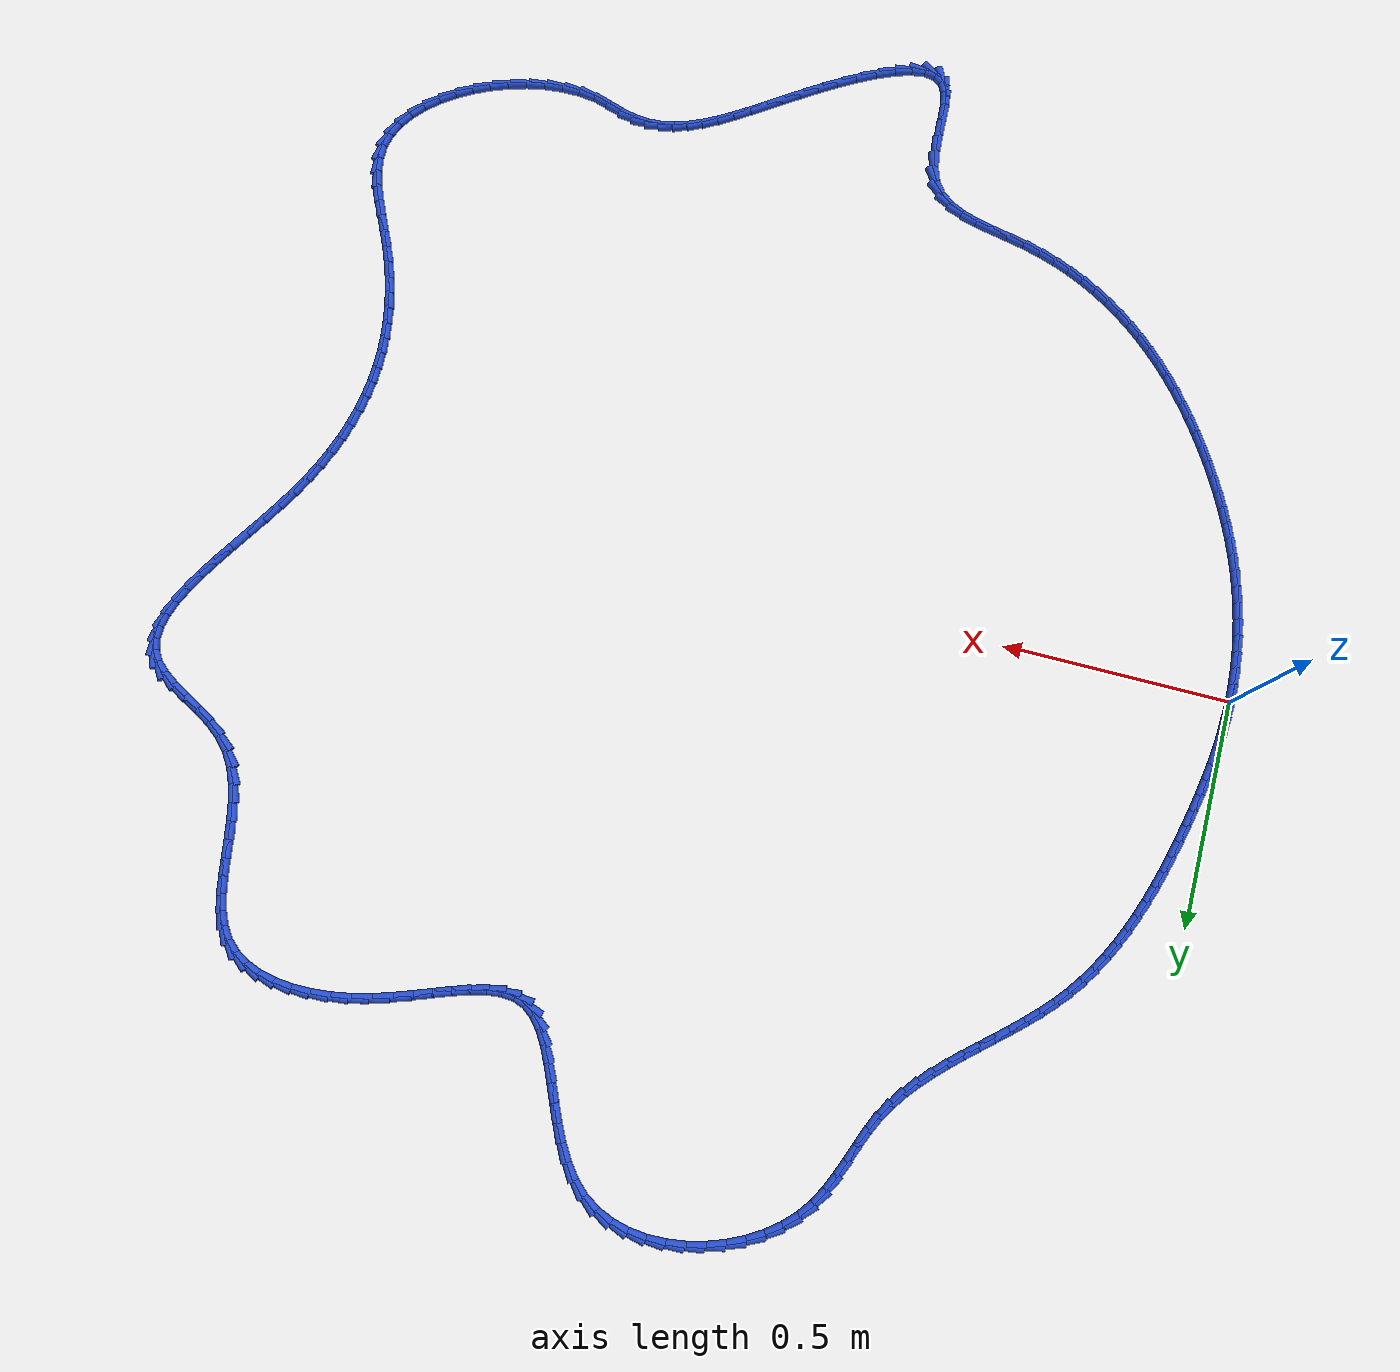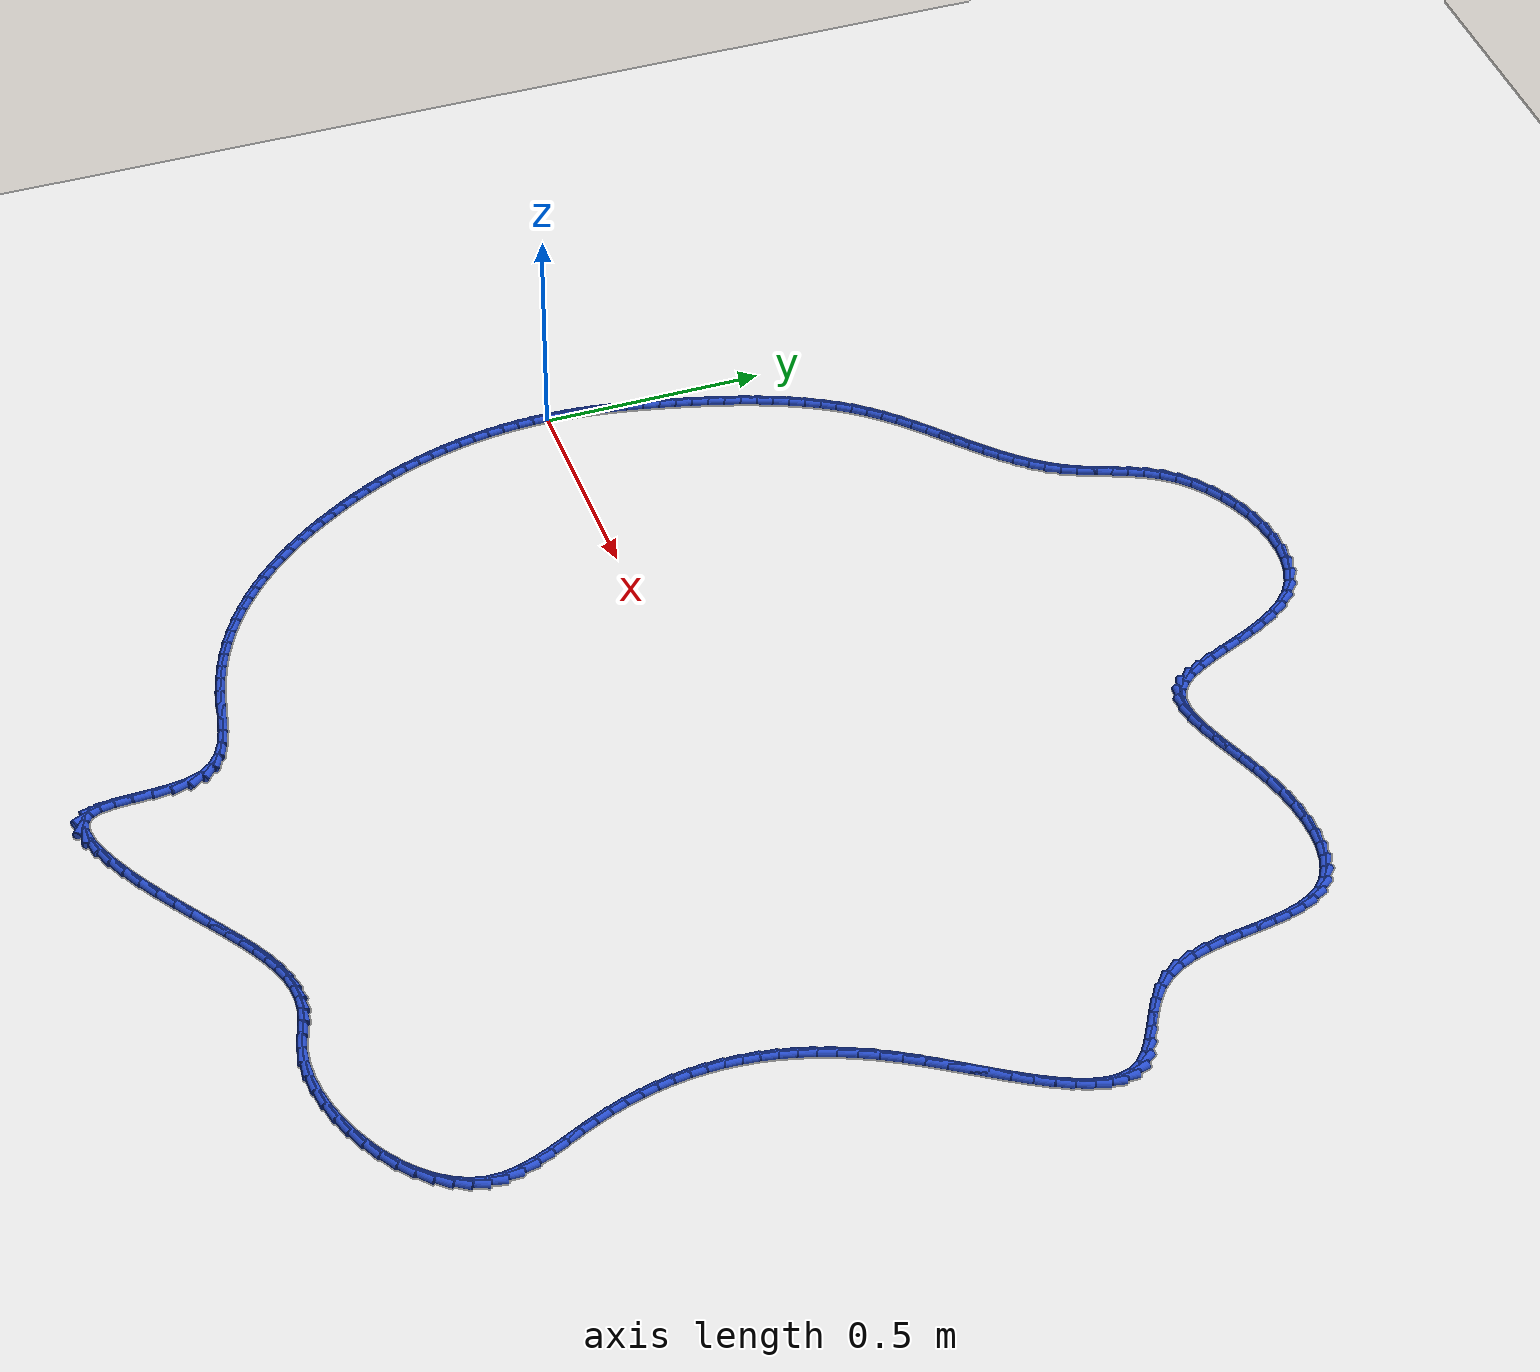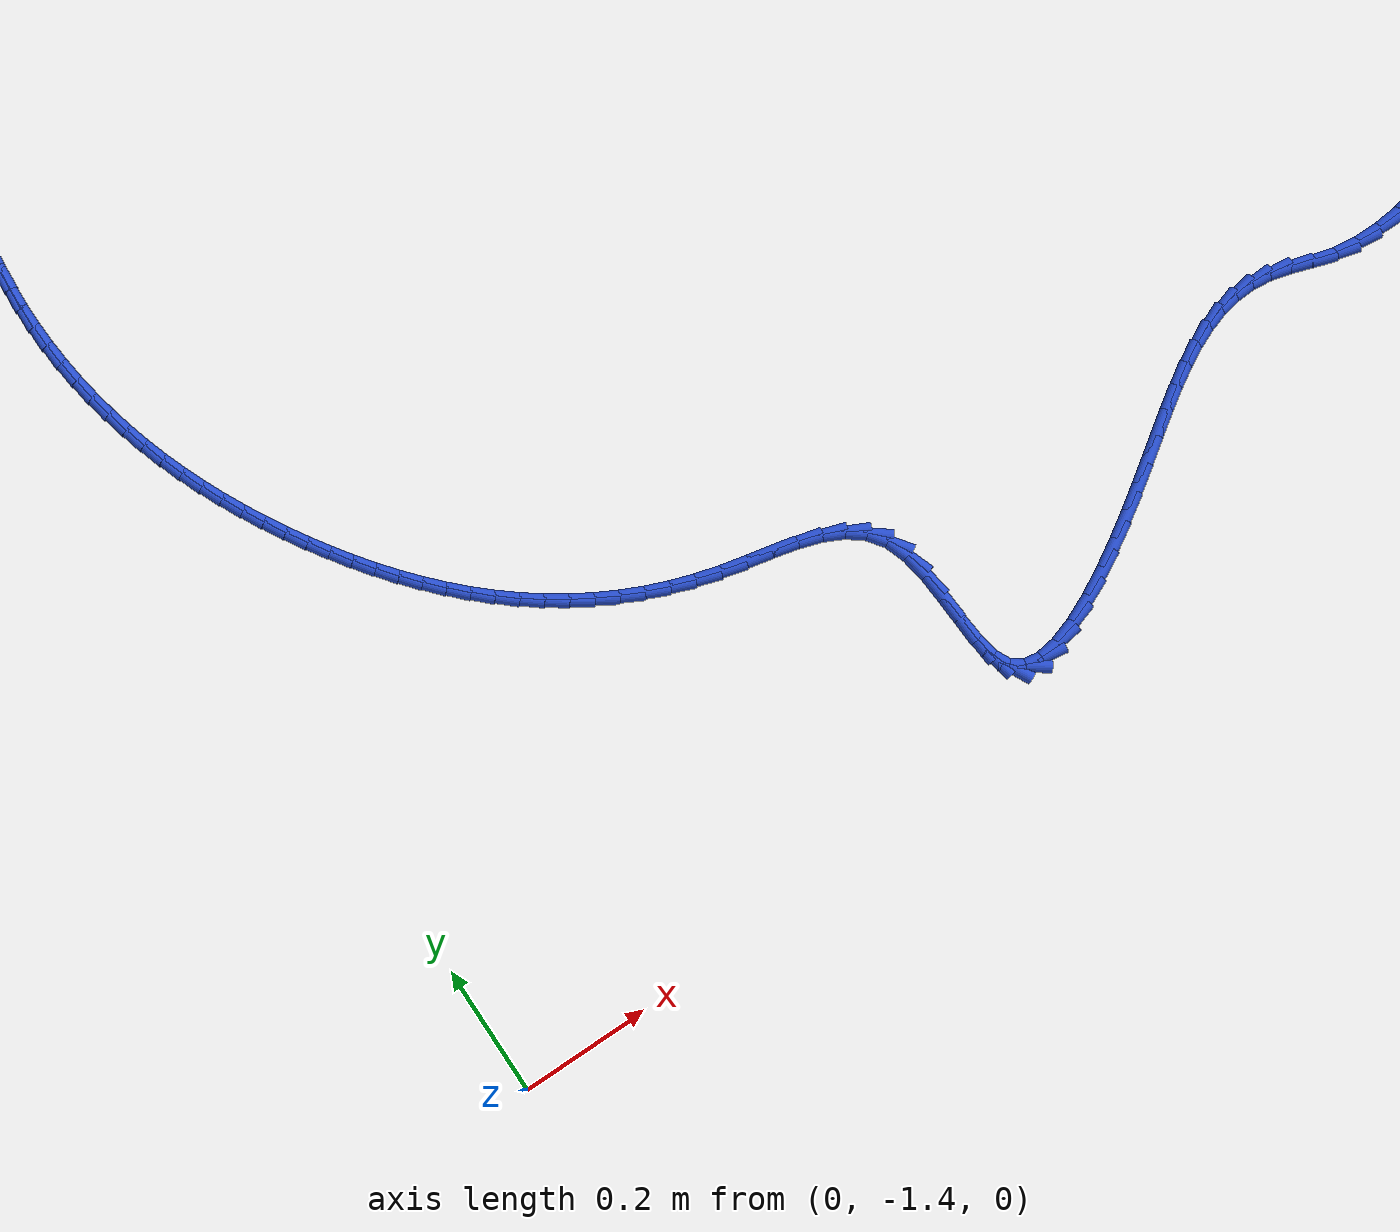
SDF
<sdf version="1.6">
 <world name="default">
  <light name="sun" type="directional">
   <pose>0 0 10 0 -0 0</pose>
   <diffuse>0.8 0.8 0.8 1</diffuse>
   <specular>0.2 0.2 0.2 1</specular>
   <attenuation>
    <range>1000</range>
    <constant>0.9</constant>
    <linear>0.01</linear>
    <quadratic>0.001</quadratic>
   </attenuation>
   <direction>-0.5 0.1 -0.9</direction>
  </light>
  <model name="ground_plane">
   <static>1</static>
   <link name="link">
    <collision name="collision">
     <geometry><plane><normal>0 0 1</normal><size>100 100</size></plane></geometry>
     <surface><friction><ode><mu>100</mu><mu2>50</mu2></ode></friction></surface>
    </collision>
    <visual name="visual">
     <cast_shadows>0</cast_shadows>
     <geometry><plane><normal>0 0 1</normal><size>100 100</size></plane></geometry>
     <material>
      <script><uri>file://media/materials/scripts/gazebo.material</uri><name>Gazebo/WhiteGlow</name></script>
     </material>
    </visual>
   </link>
  </model>
  <gravity>0 0 -9.8</gravity>
  <magnetic_field>6e-06 2.3e-05 -4.2e-05</magnetic_field>
  <atmosphere type="adiabatic"/>
  <physics name="default_physics" default="0" type="ode">
   <max_step_size>0.001</max_step_size>
   <real_time_factor>1</real_time_factor>
   <real_time_update_rate>1000</real_time_update_rate>
  </physics>
  <scene><ambient>0.4 0.4 0.4 1</ambient><background>0.7 0.7 0.7 1</background><shadows>1</shadows></scene>
  <spherical_coordinates>
   <surface_model>EARTH_WGS84</surface_model>
   <latitude_deg>0</latitude_deg>
   <longitude_deg>0</longitude_deg>
   <elevation>0</elevation>
   <heading_deg>0</heading_deg>
  </spherical_coordinates>
  <model name="line">
   <link name="link_0">
    <pose>-8.673617379884035e-18 3.469446951953614e-17 0.01 0 1.57 1.5358566611218092</pose>
    <collision name="collision">
     <geometry><cylinder><radius>0.01</radius><length>0.08</length></cylinder></geometry>
    </collision>
    <visual name="visual">
     <material>
      <script><name>Gazebo/Blue</name><uri>file://media/materials/scripts/gazebo.material</uri></script>
     </material>
     <geometry><cylinder><radius>0.01</radius><length>0.08</length></cylinder></geometry>
    </visual>
   </link>
   <link name="link_1">
    <pose>0.0012643379825934707 0.03617159533238097 0.01 0 1.57 1.4971096954893166</pose>
    <collision name="collision">
     <geometry><cylinder><radius>0.01</radius><length>0.08</length></cylinder></geometry>
    </collision>
    <visual name="visual">
     <material>
      <script><name>Gazebo/Blue</name><uri>file://media/materials/scripts/gazebo.material</uri></script>
     </material>
     <geometry><cylinder><radius>0.01</radius><length>0.08</length></cylinder></geometry>
    </visual>
   </link>
   <link name="link_2">
    <pose>0.003926747639628221 0.07223769242623723 0.01 0 1.57 1.4620322199565978</pose>
    <collision name="collision">
     <geometry><cylinder><radius>0.01</radius><length>0.08</length></cylinder></geometry>
    </collision>
    <visual name="visual">
     <material>
      <script><name>Gazebo/Blue</name><uri>file://media/materials/scripts/gazebo.material</uri></script>
     </material>
     <geometry><cylinder><radius>0.01</radius><length>0.08</length></cylinder></geometry>
    </visual>
   </link>
   <link name="link_3">
    <pose>0.00785577732934662 0.10821945682339952 0.01 0 1.57 1.4307285916348285</pose>
    <collision name="collision">
     <geometry><cylinder><radius>0.01</radius><length>0.08</length></cylinder></geometry>
    </collision>
    <visual name="visual">
     <material>
      <script><name>Gazebo/Blue</name><uri>file://media/materials/scripts/gazebo.material</uri></script>
     </material>
     <geometry><cylinder><radius>0.01</radius><length>0.08</length></cylinder></geometry>
    </visual>
   </link>
   <link name="link_4">
    <pose>0.012919975409991043 0.14413805406569852 0.01 0 1.57 1.4032489761076152</pose>
    <collision name="collision">
     <geometry><cylinder><radius>0.01</radius><length>0.08</length></cylinder></geometry>
    </collision>
    <visual name="visual">
     <material>
      <script><name>Gazebo/Blue</name><uri>file://media/materials/scripts/gazebo.material</uri></script>
     </material>
     <geometry><cylinder><radius>0.01</radius><length>0.08</length></cylinder></geometry>
    </visual>
   </link>
   <link name="link_5">
    <pose>0.018987890239803868 0.18001464969496492 0.01 0 1.57 1.3796023103163129</pose>
    <collision name="collision">
     <geometry><cylinder><radius>0.01</radius><length>0.08</length></cylinder></geometry>
    </collision>
    <visual name="visual">
     <material>
      <script><name>Gazebo/Blue</name><uri>file://media/materials/scripts/gazebo.material</uri></script>
     </material>
     <geometry><cylinder><radius>0.01</radius><length>0.08</length></cylinder></geometry>
    </visual>
   </link>
   <link name="link_6">
    <pose>0.025928070177027463 0.2158704092530294 0.01 0 1.57 1.3597684366169516</pose>
    <collision name="collision">
     <geometry><cylinder><radius>0.01</radius><length>0.08</length></cylinder></geometry>
    </collision>
    <visual name="visual">
     <material>
      <script><name>Gazebo/Blue</name><uri>file://media/materials/scripts/gazebo.material</uri></script>
     </material>
     <geometry><cylinder><radius>0.01</radius><length>0.08</length></cylinder></geometry>
    </visual>
   </link>
   <link name="link_7">
    <pose>0.033609063579904216 0.2517264982817226 0.01 0 1.57 1.34370346270668</pose>
    <collision name="collision">
     <geometry><cylinder><radius>0.01</radius><length>0.08</length></cylinder></geometry>
    </collision>
    <visual name="visual">
     <material>
      <script><name>Gazebo/Blue</name><uri>file://media/materials/scripts/gazebo.material</uri></script>
     </material>
     <geometry><cylinder><radius>0.01</radius><length>0.08</length></cylinder></geometry>
    </visual>
   </link>
   <link name="link_8">
    <pose>0.04189959529199151 0.287603987735716 0.01 0 1.57 1.329492105155803</pose>
    <collision name="collision">
     <geometry><cylinder><radius>0.01</radius><length>0.08</length></cylinder></geometry>
    </collision>
    <visual name="visual">
     <material>
      <script><name>Gazebo/Blue</name><uri>file://media/materials/scripts/gazebo.material</uri></script>
     </material>
     <geometry><cylinder><radius>0.01</radius><length>0.08</length></cylinder></geometry>
    </visual>
   </link>
   <link name="link_9">
    <pose>0.0507311949192792 0.32349028840893146 0.01 0 1.57 1.3124633714556924</pose>
    <collision name="collision">
     <geometry><cylinder><radius>0.01</radius><length>0.08</length></cylinder></geometry>
    </collision>
    <visual name="visual">
     <material>
      <script><name>Gazebo/Blue</name><uri>file://media/materials/scripts/gazebo.material</uri></script>
     </material>
     <geometry><cylinder><radius>0.01</radius><length>0.08</length></cylinder></geometry>
    </visual>
   </link>
   <link name="link_10">
    <pose>0.060190701730452795 0.359289573009359 0.01 0 1.57 1.2918390897070708</pose>
    <collision name="collision">
     <geometry><cylinder><radius>0.01</radius><length>0.08</length></cylinder></geometry>
    </collision>
    <visual name="visual">
     <material>
      <script><name>Gazebo/Blue</name><uri>file://media/materials/scripts/gazebo.material</uri></script>
     </material>
     <geometry><cylinder><radius>0.01</radius><length>0.08</length></cylinder></geometry>
    </visual>
   </link>
   <link name="link_11">
    <pose>0.07038854391236883 0.39489337178370393 0.01 0 1.57 1.267513936303608</pose>
    <collision name="collision">
     <geometry><cylinder><radius>0.01</radius><length>0.08</length></cylinder></geometry>
    </collision>
    <visual name="visual">
     <material>
      <script><name>Gazebo/Blue</name><uri>file://media/materials/scripts/gazebo.material</uri></script>
     </material>
     <geometry><cylinder><radius>0.01</radius><length>0.08</length></cylinder></geometry>
    </visual>
   </link>
   <link name="link_12">
    <pose>0.08143514965188396 0.43019321497867197 0.01 0 1.57 1.2393606936795978</pose>
    <collision name="collision">
     <geometry><cylinder><radius>0.01</radius><length>0.08</length></cylinder></geometry>
    </collision>
    <visual name="visual">
     <material>
      <script><name>Gazebo/Blue</name><uri>file://media/materials/scripts/gazebo.material</uri></script>
     </material>
     <geometry><cylinder><radius>0.01</radius><length>0.08</length></cylinder></geometry>
    </visual>
   </link>
   <link name="link_13">
    <pose>0.09344094713585474 0.46508063284096857 0.01 0 1.57 1.2072390286842873</pose>
    <collision name="collision">
     <geometry><cylinder><radius>0.01</radius><length>0.08</length></cylinder></geometry>
    </collision>
    <visual name="visual">
     <material>
      <script><name>Gazebo/Blue</name><uri>file://media/materials/scripts/gazebo.material</uri></script>
     </material>
     <geometry><cylinder><radius>0.01</radius><length>0.08</length></cylinder></geometry>
    </visual>
   </link>
   <link name="link_14">
    <pose>0.1065163645511377 0.4994471556172989 0.01 0 1.57 1.1710069696980483</pose>
    <collision name="collision">
     <geometry><cylinder><radius>0.01</radius><length>0.08</length></cylinder></geometry>
    </collision>
    <visual name="visual">
     <material>
      <script><name>Gazebo/Blue</name><uri>file://media/materials/scripts/gazebo.material</uri></script>
     </material>
     <geometry><cylinder><radius>0.01</radius><length>0.08</length></cylinder></geometry>
    </visual>
   </link>
   <link name="link_15">
    <pose>0.12077183008458946 0.5331843135543685 0.01 0 1.57 1.1305358232662344</pose>
    <collision name="collision">
     <geometry><cylinder><radius>0.01</radius><length>0.08</length></cylinder></geometry>
    </collision>
    <visual name="visual">
     <material>
      <script><name>Gazebo/Blue</name><uri>file://media/materials/scripts/gazebo.material</uri></script>
     </material>
     <geometry><cylinder><radius>0.01</radius><length>0.08</length></cylinder></geometry>
    </visual>
   </link>
   <link name="link_16">
    <pose>0.13631777192306663 0.5661836368988831 0.01 0 1.57 1.0857290788391851</pose>
    <collision name="collision">
     <geometry><cylinder><radius>0.01</radius><length>0.08</length></cylinder></geometry>
    </collision>
    <visual name="visual">
     <material>
      <script><name>Gazebo/Blue</name><uri>file://media/materials/scripts/gazebo.material</uri></script>
     </material>
     <geometry><cylinder><radius>0.01</radius><length>0.08</length></cylinder></geometry>
    </visual>
   </link>
   <link name="link_17">
    <pose>0.1532646182534258 0.5983366558975481 0.01 0 1.57 1.036545389994959</pose>
    <collision name="collision">
     <geometry><cylinder><radius>0.01</radius><length>0.08</length></cylinder></geometry>
    </collision>
    <visual name="visual">
     <material>
      <script><name>Gazebo/Blue</name><uri>file://media/materials/scripts/gazebo.material</uri></script>
     </material>
     <geometry><cylinder><radius>0.01</radius><length>0.08</length></cylinder></geometry>
    </visual>
   </link>
   <link name="link_18">
    <pose>0.17172279726252346 0.6295349007970688 0.01 0 1.57 0.9830248916050008</pose>
    <collision name="collision">
     <geometry><cylinder><radius>0.01</radius><length>0.08</length></cylinder></geometry>
    </collision>
    <visual name="visual">
     <material>
      <script><name>Gazebo/Blue</name><uri>file://media/materials/scripts/gazebo.material</uri></script>
     </material>
     <geometry><cylinder><radius>0.01</radius><length>0.08</length></cylinder></geometry>
    </visual>
   </link>
   <link name="link_19">
    <pose>0.1918027371372162 0.6596699018441504 0.01 0 1.57 0.9253168748304635</pose>
    <collision name="collision">
     <geometry><cylinder><radius>0.01</radius><length>0.08</length></cylinder></geometry>
    </collision>
    <visual name="visual">
     <material>
      <script><name>Gazebo/Blue</name><uri>file://media/materials/scripts/gazebo.material</uri></script>
     </material>
     <geometry><cylinder><radius>0.01</radius><length>0.08</length></cylinder></geometry>
    </visual>
   </link>
   <link name="link_20">
    <pose>0.21361486606436075 0.688633189285499 0.01 0 1.57 0.8646955293794278</pose>
    <collision name="collision">
     <geometry><cylinder><radius>0.01</radius><length>0.08</length></cylinder></geometry>
    </collision>
    <visual name="visual">
     <material>
      <script><name>Gazebo/Blue</name><uri>file://media/materials/scripts/gazebo.material</uri></script>
     </material>
     <geometry><cylinder><radius>0.01</radius><length>0.08</length></cylinder></geometry>
    </visual>
   </link>
   <link name="link_21">
    <pose>0.23724048459426914 0.7163377053367608 0.01 0 1.57 0.8111253378330151</pose>
    <collision name="collision">
     <geometry><cylinder><radius>0.01</radius><length>0.08</length></cylinder></geometry>
    </collision>
    <visual name="visual">
     <material>
      <script><name>Gazebo/Blue</name><uri>file://media/materials/scripts/gazebo.material</uri></script>
     </material>
     <geometry><cylinder><radius>0.01</radius><length>0.08</length></cylinder></geometry>
    </visual>
   </link>
   <link name="link_22">
    <pose>0.2624757380812664 0.7429060121801943 0.01 0 1.57 0.7699388440663362</pose>
    <collision name="collision">
     <geometry><cylinder><radius>0.01</radius><length>0.08</length></cylinder></geometry>
    </collision>
    <visual name="visual">
     <material>
      <script><name>Gazebo/Blue</name><uri>file://media/materials/scripts/gazebo.material</uri></script>
     </material>
     <geometry><cylinder><radius>0.01</radius><length>0.08</length></cylinder></geometry>
    </visual>
   </link>
   <link name="link_23">
    <pose>0.28895536361723695 0.7685793245601015 0.01 0 1.57 0.7408283443323731</pose>
    <collision name="collision">
     <geometry><cylinder><radius>0.01</radius><length>0.08</length></cylinder></geometry>
    </collision>
    <visual name="visual">
     <material>
      <script><name>Gazebo/Blue</name><uri>file://media/materials/scripts/gazebo.material</uri></script>
     </material>
     <geometry><cylinder><radius>0.01</radius><length>0.08</length></cylinder></geometry>
    </visual>
   </link>
   <link name="link_24">
    <pose>0.31631226164230225 0.7936002073588365 0.01 0 1.57 0.7234316500924773</pose>
    <collision name="collision">
     <geometry><cylinder><radius>0.01</radius><length>0.08</length></cylinder></geometry>
    </collision>
    <visual name="visual">
     <material>
      <script><name>Gazebo/Blue</name><uri>file://media/materials/scripts/gazebo.material</uri></script>
     </material>
     <geometry><cylinder><radius>0.01</radius><length>0.08</length></cylinder></geometry>
    </visual>
   </link>
   <link name="link_25">
    <pose>0.34417933259658384 0.8182112254587547 0.01 0 1.57 0.7175109697583758</pose>
    <collision name="collision">
     <geometry><cylinder><radius>0.01</radius><length>0.08</length></cylinder></geometry>
    </collision>
    <visual name="visual">
     <material>
      <script><name>Gazebo/Blue</name><uri>file://media/materials/scripts/gazebo.material</uri></script>
     </material>
     <geometry><cylinder><radius>0.01</radius><length>0.08</length></cylinder></geometry>
    </visual>
   </link>
   <link name="link_26">
    <pose>0.37218947692020293 0.8426549437422098 0.01 0 1.57 0.7230161860961923</pose>
    <collision name="collision">
     <geometry><cylinder><radius>0.01</radius><length>0.08</length></cylinder></geometry>
    </collision>
    <visual name="visual">
     <material>
      <script><name>Gazebo/Blue</name><uri>file://media/materials/scripts/gazebo.material</uri></script>
     </material>
     <geometry><cylinder><radius>0.01</radius><length>0.08</length></cylinder></geometry>
    </visual>
   </link>
   <link name="link_27">
    <pose>0.39997559505328134 0.8671739270915578 0.01 0 1.57 0.740107279914569</pose>
    <collision name="collision">
     <geometry><cylinder><radius>0.01</radius><length>0.08</length></cylinder></geometry>
    </collision>
    <visual name="visual">
     <material>
      <script><name>Gazebo/Blue</name><uri>file://media/materials/scripts/gazebo.material</uri></script>
     </material>
     <geometry><cylinder><radius>0.01</radius><length>0.08</length></cylinder></geometry>
    </visual>
   </link>
   <link name="link_28">
    <pose>0.42717058743594016 0.8920107403891522 0.01 0 1.57 0.7691397799463697</pose>
    <collision name="collision">
     <geometry><cylinder><radius>0.01</radius><length>0.08</length></cylinder></geometry>
    </collision>
    <visual name="visual">
     <material>
      <script><name>Gazebo/Blue</name><uri>file://media/materials/scripts/gazebo.material</uri></script>
     </material>
     <geometry><cylinder><radius>0.01</radius><length>0.08</length></cylinder></geometry>
    </visual>
   </link>
   <link name="link_29">
    <pose>0.45340735450830133 0.9174079485173486 0.01 0 1.57 0.8106067733869036</pose>
    <collision name="collision">
     <geometry><cylinder><radius>0.01</radius><length>0.08</length></cylinder></geometry>
    </collision>
    <visual name="visual">
     <material>
      <script><name>Gazebo/Blue</name><uri>file://media/materials/scripts/gazebo.material</uri></script>
     </material>
     <geometry><cylinder><radius>0.01</radius><length>0.08</length></cylinder></geometry>
    </visual>
   </link>
   <link name="link_30">
    <pose>0.4783187967104858 0.9436081163585008 0.01 0 1.57 0.8650213602774097</pose>
    <collision name="collision">
     <geometry><cylinder><radius>0.01</radius><length>0.08</length></cylinder></geometry>
    </collision>
    <visual name="visual">
     <material>
      <script><name>Gazebo/Blue</name><uri>file://media/materials/scripts/gazebo.material</uri></script>
     </material>
     <geometry><cylinder><radius>0.01</radius><length>0.08</length></cylinder></geometry>
    </visual>
   </link>
   <link name="link_31">
    <pose>0.5015378144826155 0.970853808794965 0.01 0 1.57 0.9327191332742362</pose>
    <collision name="collision">
     <geometry><cylinder><radius>0.01</radius><length>0.08</length></cylinder></geometry>
    </collision>
    <visual name="visual">
     <material>
      <script><name>Gazebo/Blue</name><uri>file://media/materials/scripts/gazebo.material</uri></script>
     </material>
     <geometry><cylinder><radius>0.01</radius><length>0.08</length></cylinder></geometry>
    </visual>
   </link>
   <link name="link_32">
    <pose>0.5226973082648116 0.9993875907090944 0.01 0 1.57 1.013571179386667</pose>
    <collision name="collision">
     <geometry><cylinder><radius>0.01</radius><length>0.08</length></cylinder></geometry>
    </collision>
    <visual name="visual">
     <material>
      <script><name>Gazebo/Blue</name><uri>file://media/materials/scripts/gazebo.material</uri></script>
     </material>
     <geometry><cylinder><radius>0.01</radius><length>0.08</length></cylinder></geometry>
    </visual>
   </link>
   <link name="link_33">
    <pose>0.5414301784971958 1.0294520269832448 0.01 0 1.57 1.1042354680259792</pose>
    <collision name="collision">
     <geometry><cylinder><radius>0.01</radius><length>0.08</length></cylinder></geometry>
    </collision>
    <visual name="visual">
     <material>
      <script><name>Gazebo/Blue</name><uri>file://media/materials/scripts/gazebo.material</uri></script>
     </material>
     <geometry><cylinder><radius>0.01</radius><length>0.08</length></cylinder></geometry>
    </visual>
   </link>
   <link name="link_34">
    <pose>0.5574436880247429 1.0612471398191636 0.01 0 1.57 1.1734823656794087</pose>
    <collision name="collision">
     <geometry><cylinder><radius>0.01</radius><length>0.08</length></cylinder></geometry>
    </collision>
    <visual name="visual">
     <material>
      <script><name>Gazebo/Blue</name><uri>file://media/materials/scripts/gazebo.material</uri></script>
     </material>
     <geometry><cylinder><radius>0.01</radius><length>0.08</length></cylinder></geometry>
    </visual>
   </link>
   <link name="link_35">
    <pose>0.5713732499692051 1.0944419572844328 0.01 0 1.57 1.2017743278868716</pose>
    <collision name="collision">
     <geometry><cylinder><radius>0.01</radius><length>0.08</length></cylinder></geometry>
    </collision>
    <visual name="visual">
     <material>
      <script><name>Gazebo/Blue</name><uri>file://media/materials/scripts/gazebo.material</uri></script>
     </material>
     <geometry><cylinder><radius>0.01</radius><length>0.08</length></cylinder></geometry>
    </visual>
   </link>
   <link name="link_36">
    <pose>0.5844847817057239 1.1283447963974718 0.01 0 1.57 1.190123981029735</pose>
    <collision name="collision">
     <geometry><cylinder><radius>0.01</radius><length>0.08</length></cylinder></geometry>
    </collision>
    <visual name="visual">
     <material>
      <script><name>Gazebo/Blue</name><uri>file://media/materials/scripts/gazebo.material</uri></script>
     </material>
     <geometry><cylinder><radius>0.01</radius><length>0.08</length></cylinder></geometry>
    </visual>
   </link>
   <link name="link_37">
    <pose>0.5980562294849665 1.1622570924652948 0.01 0 1.57 1.1389958916644605</pose>
    <collision name="collision">
     <geometry><cylinder><radius>0.01</radius><length>0.08</length></cylinder></geometry>
    </collision>
    <visual name="visual">
     <material>
      <script><name>Gazebo/Blue</name><uri>file://media/materials/scripts/gazebo.material</uri></script>
     </material>
     <geometry><cylinder><radius>0.01</radius><length>0.08</length></cylinder></geometry>
    </visual>
   </link>
   <link name="link_38">
    <pose>0.6133655395575996 1.195480280794916 0.01 0 1.57 1.0484971937694696</pose>
    <collision name="collision">
     <geometry><cylinder><radius>0.01</radius><length>0.08</length></cylinder></geometry>
    </collision>
    <visual name="visual">
     <material>
      <script><name>Gazebo/Blue</name><uri>file://media/materials/scripts/gazebo.material</uri></script>
     </material>
     <geometry><cylinder><radius>0.01</radius><length>0.08</length></cylinder></geometry>
    </visual>
   </link>
   <link name="link_39">
    <pose>0.6316906581742908 1.2273157966933503 0.01 0 1.57 0.921144690310347</pose>
    <collision name="collision">
     <geometry><cylinder><radius>0.01</radius><length>0.08</length></cylinder></geometry>
    </collision>
    <visual name="visual">
     <material>
      <script><name>Gazebo/Blue</name><uri>file://media/materials/scripts/gazebo.material</uri></script>
     </material>
     <geometry><cylinder><radius>0.01</radius><length>0.08</length></cylinder></geometry>
    </visual>
   </link>
   <link name="link_40">
    <pose>0.6542925485223795 1.2570686378772085 0.01 0 1.57 0.7817355829819229</pose>
    <collision name="collision">
     <geometry><cylinder><radius>0.01</radius><length>0.08</length></cylinder></geometry>
    </collision>
    <visual name="visual">
     <material>
      <script><name>Gazebo/Blue</name><uri>file://media/materials/scripts/gazebo.material</uri></script>
     </material>
     <geometry><cylinder><radius>0.01</radius><length>0.08</length></cylinder></geometry>
    </visual>
   </link>
   <link name="link_41">
    <pose>0.6816345739705377 1.2842111085844885 0.01 0 1.57 0.6570782064253526</pose>
    <collision name="collision">
     <geometry><cylinder><radius>0.01</radius><length>0.08</length></cylinder></geometry>
    </collision>
    <visual name="visual">
     <material>
      <script><name>Gazebo/Blue</name><uri>file://media/materials/scripts/gazebo.material</uri></script>
     </material>
     <geometry><cylinder><radius>0.01</radius><length>0.08</length></cylinder></geometry>
    </visual>
   </link>
   <link name="link_42">
    <pose>0.7130566607372467 1.3084511680235122 0.01 0 1.57 0.544825665864811</pose>
    <collision name="collision">
     <geometry><cylinder><radius>0.01</radius><length>0.08</length></cylinder></geometry>
    </collision>
    <visual name="visual">
     <material>
      <script><name>Gazebo/Blue</name><uri>file://media/materials/scripts/gazebo.material</uri></script>
     </material>
     <geometry><cylinder><radius>0.01</radius><length>0.08</length></cylinder></geometry>
    </visual>
   </link>
   <link name="link_43">
    <pose>0.7478141780476387 1.3295145122877952 0.01 0 1.57 0.4406455929869234</pose>
    <collision name="collision">
     <geometry><cylinder><radius>0.01</radius><length>0.08</length></cylinder></geometry>
    </collision>
    <visual name="visual">
     <material>
      <script><name>Gazebo/Blue</name><uri>file://media/materials/scripts/gazebo.material</uri></script>
     </material>
     <geometry><cylinder><radius>0.01</radius><length>0.08</length></cylinder></geometry>
    </visual>
   </link>
   <link name="link_44">
    <pose>0.7851624951268471 1.3471268374708545 0.01 0 1.57 0.3405093780962412</pose>
    <collision name="collision">
     <geometry><cylinder><radius>0.01</radius><length>0.08</length></cylinder></geometry>
    </collision>
    <visual name="visual">
     <material>
      <script><name>Gazebo/Blue</name><uri>file://media/materials/scripts/gazebo.material</uri></script>
     </material>
     <geometry><cylinder><radius>0.01</radius><length>0.08</length></cylinder></geometry>
    </visual>
   </link>
   <link name="link_45">
    <pose>0.8243569812000046 1.3610138396662066 0.01 0 1.57 0.24061488266578748</pose>
    <collision name="collision">
     <geometry><cylinder><radius>0.01</radius><length>0.08</length></cylinder></geometry>
    </collision>
    <visual name="visual">
     <material>
      <script><name>Gazebo/Blue</name><uri>file://media/materials/scripts/gazebo.material</uri></script>
     </material>
     <geometry><cylinder><radius>0.01</radius><length>0.08</length></cylinder></geometry>
    </visual>
   </link>
   <link name="link_46">
    <pose>0.8646530054922443 1.370901214967368 0.01 0 1.57 0.13721447231933942</pose>
    <collision name="collision">
     <geometry><cylinder><radius>0.01</radius><length>0.08</length></cylinder></geometry>
    </collision>
    <visual name="visual">
     <material>
      <script><name>Gazebo/Blue</name><uri>file://media/materials/scripts/gazebo.material</uri></script>
     </material>
     <geometry><cylinder><radius>0.01</radius><length>0.08</length></cylinder></geometry>
    </visual>
   </link>
   <link name="link_47">
    <pose>0.9053059372286996 1.3765146594678557 0.01 0 1.57 0.026448674699358313</pose>
    <collision name="collision">
     <geometry><cylinder><radius>0.01</radius><length>0.08</length></cylinder></geometry>
    </collision>
    <visual name="visual">
     <material>
      <script><name>Gazebo/Blue</name><uri>file://media/materials/scripts/gazebo.material</uri></script>
     </material>
     <geometry><cylinder><radius>0.01</radius><length>0.08</length></cylinder></geometry>
    </visual>
   </link>
   <link name="link_48">
    <pose>0.9455711456345031 1.3775798692611856 0.01 0 1.57 -0.0957212625487064</pose>
    <collision name="collision">
     <geometry><cylinder><radius>0.01</radius><length>0.08</length></cylinder></geometry>
    </collision>
    <visual name="visual">
     <material>
      <script><name>Gazebo/Blue</name><uri>file://media/materials/scripts/gazebo.material</uri></script>
     </material>
     <geometry><cylinder><radius>0.01</radius><length>0.08</length></cylinder></geometry>
    </visual>
   </link>
   <link name="link_49">
    <pose>0.984703999934788 1.3738225404408748 0.01 0 1.57 -0.2333297636257535</pose>
    <collision name="collision">
     <geometry><cylinder><radius>0.01</radius><length>0.08</length></cylinder></geometry>
    </collision>
    <visual name="visual">
     <material>
      <script><name>Gazebo/Blue</name><uri>file://media/materials/scripts/gazebo.material</uri></script>
     </material>
     <geometry><cylinder><radius>0.01</radius><length>0.08</length></cylinder></geometry>
    </visual>
   </link>
   <link name="link_50">
    <pose>1.0219598693546872 1.3649683691004397 0.01 0 1.57 -0.3897217880723271</pose>
    <collision name="collision">
     <geometry><cylinder><radius>0.01</radius><length>0.08</length></cylinder></geometry>
    </collision>
    <visual name="visual">
     <material>
      <script><name>Gazebo/Blue</name><uri>file://media/materials/scripts/gazebo.material</uri></script>
     </material>
     <geometry><cylinder><radius>0.01</radius><length>0.08</length></cylinder></geometry>
    </visual>
   </link>
   <link name="link_51">
    <pose>1.0565941231193339 1.3507430513333967 0.01 0 1.57 -0.5661131193277678</pose>
    <collision name="collision">
     <geometry><cylinder><radius>0.01</radius><length>0.08</length></cylinder></geometry>
    </collision>
    <visual name="visual">
     <material>
      <script><name>Gazebo/Blue</name><uri>file://media/materials/scripts/gazebo.material</uri></script>
     </material>
     <geometry><cylinder><radius>0.01</radius><length>0.08</length></cylinder></geometry>
    </visual>
   </link>
   <link name="link_52">
    <pose>1.0878621304538605 1.3308722832332625 0.01 0 1.57 -0.7528160501932751</pose>
    <collision name="collision">
     <geometry><cylinder><radius>0.01</radius><length>0.08</length></cylinder></geometry>
    </collision>
    <visual name="visual">
     <material>
      <script><name>Gazebo/Blue</name><uri>file://media/materials/scripts/gazebo.material</uri></script>
     </material>
     <geometry><cylinder><radius>0.01</radius><length>0.08</length></cylinder></geometry>
    </visual>
   </link>
   <link name="link_53">
    <pose>1.1151919186763366 1.3052678155038229 0.01 0 1.57 -0.9076844818424412</pose>
    <collision name="collision">
     <geometry><cylinder><radius>0.01</radius><length>0.08</length></cylinder></geometry>
    </collision>
    <visual name="visual">
     <material>
      <script><name>Gazebo/Blue</name><uri>file://media/materials/scripts/gazebo.material</uri></script>
     </material>
     <geometry><cylinder><radius>0.01</radius><length>0.08</length></cylinder></geometry>
    </visual>
   </link>
   <link name="link_54">
    <pose>1.138949599904561 1.2748522695172781 0.01 0 1.57 -1.0198065131820249</pose>
    <collision name="collision">
     <geometry><cylinder><radius>0.01</radius><length>0.08</length></cylinder></geometry>
    </collision>
    <visual name="visual">
     <material>
      <script><name>Gazebo/Blue</name><uri>file://media/materials/scripts/gazebo.material</uri></script>
     </material>
     <geometry><cylinder><radius>0.01</radius><length>0.08</length></cylinder></geometry>
    </visual>
   </link>
   <link name="link_55">
    <pose>1.1598183604236978 1.240889942553588 0.01 0 1.57 -1.0952789635245899</pose>
    <collision name="collision">
     <geometry><cylinder><radius>0.01</radius><length>0.08</length></cylinder></geometry>
    </collision>
    <visual name="visual">
     <material>
      <script><name>Gazebo/Blue</name><uri>file://media/materials/scripts/gazebo.material</uri></script>
     </material>
     <geometry><cylinder><radius>0.01</radius><length>0.08</length></cylinder></geometry>
    </visual>
   </link>
   <link name="link_56">
    <pose>1.178481635220568 1.204645399891093 0.01 0 1.57 -1.139643958567472</pose>
    <collision name="collision">
     <geometry><cylinder><radius>0.01</radius><length>0.08</length></cylinder></geometry>
    </collision>
    <visual name="visual">
     <material>
      <script><name>Gazebo/Blue</name><uri>file://media/materials/scripts/gazebo.material</uri></script>
     </material>
     <geometry><cylinder><radius>0.01</radius><length>0.08</length></cylinder></geometry>
    </visual>
   </link>
   <link name="link_57">
    <pose>1.1956228592819902 1.1673832068081333 0.01 0 1.57 -1.1559299487257806</pose>
    <collision name="collision">
     <geometry><cylinder><radius>0.01</radius><length>0.08</length></cylinder></geometry>
    </collision>
    <visual name="visual">
     <material>
      <script><name>Gazebo/Blue</name><uri>file://media/materials/scripts/gazebo.material</uri></script>
     </material>
     <geometry><cylinder><radius>0.01</radius><length>0.08</length></cylinder></geometry>
    </visual>
   </link>
   <link name="link_58">
    <pose>1.2119254675947835 1.1303679285830492 0.01 0 1.57 -1.1439508892380683</pose>
    <collision name="collision">
     <geometry><cylinder><radius>0.01</radius><length>0.08</length></cylinder></geometry>
    </collision>
    <visual name="visual">
     <material>
      <script><name>Gazebo/Blue</name><uri>file://media/materials/scripts/gazebo.material</uri></script>
     </material>
     <geometry><cylinder><radius>0.01</radius><length>0.08</length></cylinder></geometry>
    </visual>
   </link>
   <link name="link_59">
    <pose>1.2280728951457678 1.0948641304941802 0.01 0 1.57 -1.0995560003882805</pose>
    <collision name="collision">
     <geometry><cylinder><radius>0.01</radius><length>0.08</length></cylinder></geometry>
    </collision>
    <visual name="visual">
     <material>
      <script><name>Gazebo/Blue</name><uri>file://media/materials/scripts/gazebo.material</uri></script>
     </material>
     <geometry><cylinder><radius>0.01</radius><length>0.08</length></cylinder></geometry>
    </visual>
   </link>
   <link name="link_60">
    <pose>1.2447485769217619 1.0621363778198678 0.01 0 1.57 -1.0132528471072597</pose>
    <collision name="collision">
     <geometry><cylinder><radius>0.01</radius><length>0.08</length></cylinder></geometry>
    </collision>
    <visual name="visual">
     <material>
      <script><name>Gazebo/Blue</name><uri>file://media/materials/scripts/gazebo.material</uri></script>
     </material>
     <geometry><cylinder><radius>0.01</radius><length>0.08</length></cylinder></geometry>
    </visual>
   </link>
   <link name="link_61">
    <pose>1.2626359479095854 1.033449235838451 0.01 0 1.57 -0.8685953580897825</pose>
    <collision name="collision">
     <geometry><cylinder><radius>0.01</radius><length>0.08</length></cylinder></geometry>
    </collision>
    <visual name="visual">
     <material>
      <script><name>Gazebo/Blue</name><uri>file://media/materials/scripts/gazebo.material</uri></script>
     </material>
     <geometry><cylinder><radius>0.01</radius><length>0.08</length></cylinder></geometry>
    </visual>
   </link>
   <link name="link_62">
    <pose>1.2824184430960577 1.0100672698282716 0.01 0 1.57 -0.6446859443125712</pose>
    <collision name="collision">
     <geometry><cylinder><radius>0.01</radius><length>0.08</length></cylinder></geometry>
    </collision>
    <visual name="visual">
     <material>
      <script><name>Gazebo/Blue</name><uri>file://media/materials/scripts/gazebo.material</uri></script>
     </material>
     <geometry><cylinder><radius>0.01</radius><length>0.08</length></cylinder></geometry>
    </visual>
   </link>
   <link name="link_63">
    <pose>1.304779497467998 0.9932550450676679 0.01 0 1.57 -0.34712787269608547</pose>
    <collision name="collision">
     <geometry><cylinder><radius>0.01</radius><length>0.08</length></cylinder></geometry>
    </collision>
    <visual name="visual">
     <material>
      <script><name>Gazebo/Blue</name><uri>file://media/materials/scripts/gazebo.material</uri></script>
     </material>
     <geometry><cylinder><radius>0.01</radius><length>0.08</length></cylinder></geometry>
    </visual>
   </link>
   <link name="link_64">
    <pose>1.3303003104585671 0.9840222001581458 0.01 0 1.57 -0.07807522598313596</pose>
    <collision name="collision">
     <geometry><cylinder><radius>0.01</radius><length>0.08</length></cylinder></geometry>
    </collision>
    <visual name="visual">
     <material>
      <script><name>Gazebo/Blue</name><uri>file://media/materials/scripts/gazebo.material</uri></script>
     </material>
     <geometry><cylinder><radius>0.01</radius><length>0.08</length></cylinder></geometry>
    </visual>
   </link>
   <link name="link_65">
    <pose>1.358922267383465 0.9817829826565025 0.01 0 1.57 0.1126037953044279</pose>
    <collision name="collision">
     <geometry><cylinder><radius>0.01</radius><length>0.08</length></cylinder></geometry>
    </collision>
    <visual name="visual">
     <material>
      <script><name>Gazebo/Blue</name><uri>file://media/materials/scripts/gazebo.material</uri></script>
     </material>
     <geometry><cylinder><radius>0.01</radius><length>0.08</length></cylinder></geometry>
    </visual>
   </link>
   <link name="link_66">
    <pose>1.3903397533080506 0.9853357393810549 0.01 0 1.57 0.23565966130081162</pose>
    <collision name="collision">
     <geometry><cylinder><radius>0.01</radius><length>0.08</length></cylinder></geometry>
    </collision>
    <visual name="visual">
     <material>
      <script><name>Gazebo/Blue</name><uri>file://media/materials/scripts/gazebo.material</uri></script>
     </material>
     <geometry><cylinder><radius>0.01</radius><length>0.08</length></cylinder></geometry>
    </visual>
   </link>
   <link name="link_67">
    <pose>1.4242466255802237 0.9934775012746451 0.01 0 1.57 0.30917404496661555</pose>
    <collision name="collision">
     <geometry><cylinder><radius>0.01</radius><length>0.08</length></cylinder></geometry>
    </collision>
    <visual name="visual">
     <material>
      <script><name>Gazebo/Blue</name><uri>file://media/materials/scripts/gazebo.material</uri></script>
     </material>
     <geometry><cylinder><radius>0.01</radius><length>0.08</length></cylinder></geometry>
    </visual>
   </link>
   <link name="link_68">
    <pose>1.4603367415478867 1.005005299280116 0.01 0 1.57 0.3465500750092205</pose>
    <collision name="collision">
     <geometry><cylinder><radius>0.01</radius><length>0.08</length></cylinder></geometry>
    </collision>
    <visual name="visual">
     <material>
      <script><name>Gazebo/Blue</name><uri>file://media/materials/scripts/gazebo.material</uri></script>
     </material>
     <geometry><cylinder><radius>0.01</radius><length>0.08</length></cylinder></geometry>
    </visual>
   </link>
   <link name="link_69">
    <pose>1.4983039585589404 1.0187161643403104 0.01 0 1.57 0.3557548991404628</pose>
    <collision name="collision">
     <geometry><cylinder><radius>0.01</radius><length>0.08</length></cylinder></geometry>
    </collision>
    <visual name="visual">
     <material>
      <script><name>Gazebo/Blue</name><uri>file://media/materials/scripts/gazebo.material</uri></script>
     </material>
     <geometry><cylinder><radius>0.01</radius><length>0.08</length></cylinder></geometry>
    </visual>
   </link>
   <link name="link_70">
    <pose>1.5378421339612864 1.0334071273980712 0.01 0 1.57 0.3407528009899024</pose>
    <collision name="collision">
     <geometry><cylinder><radius>0.01</radius><length>0.08</length></cylinder></geometry>
    </collision>
    <visual name="visual">
     <material>
      <script><name>Gazebo/Blue</name><uri>file://media/materials/scripts/gazebo.material</uri></script>
     </material>
     <geometry><cylinder><radius>0.01</radius><length>0.08</length></cylinder></geometry>
    </visual>
   </link>
   <link name="link_71">
    <pose>1.5786451251028253 1.0478752193962404 0.01 0 1.57 0.30270448738215494</pose>
    <collision name="collision">
     <geometry><cylinder><radius>0.01</radius><length>0.08</length></cylinder></geometry>
    </collision>
    <visual name="visual">
     <material>
      <script><name>Gazebo/Blue</name><uri>file://media/materials/scripts/gazebo.material</uri></script>
     </material>
     <geometry><cylinder><radius>0.01</radius><length>0.08</length></cylinder></geometry>
    </visual>
   </link>
   <link name="link_72">
    <pose>1.62040678933146 1.0609174712776617 0.01 0 1.57 0.24243834349626506</pose>
    <collision name="collision">
     <geometry><cylinder><radius>0.01</radius><length>0.08</length></cylinder></geometry>
    </collision>
    <visual name="visual">
     <material>
      <script><name>Gazebo/Blue</name><uri>file://media/materials/scripts/gazebo.material</uri></script>
     </material>
     <geometry><cylinder><radius>0.01</radius><length>0.08</length></cylinder></geometry>
    </visual>
   </link>
   <link name="link_73">
    <pose>1.6627934653189038 1.0713998072025657 0.01 0 1.57 0.17215603265799068</pose>
    <collision name="collision">
     <geometry><cylinder><radius>0.01</radius><length>0.08</length></cylinder></geometry>
    </collision>
    <visual name="visual">
     <material>
      <script><name>Gazebo/Blue</name><uri>file://media/materials/scripts/gazebo.material</uri></script>
     </material>
     <geometry><cylinder><radius>0.01</radius><length>0.08</length></cylinder></geometry>
    </visual>
   </link>
   <link name="link_74">
    <pose>1.7052352940850517 1.078779473968361 0.01 0 1.57 0.09622256669749692</pose>
    <collision name="collision">
     <geometry><cylinder><radius>0.01</radius><length>0.08</length></cylinder></geometry>
    </collision>
    <visual name="visual">
     <material>
      <script><name>Gazebo/Blue</name><uri>file://media/materials/scripts/gazebo.material</uri></script>
     </material>
     <geometry><cylinder><radius>0.01</radius><length>0.08</length></cylinder></geometry>
    </visual>
   </link>
   <link name="link_75">
    <pose>1.7470421917133776 1.082814702425044 0.01 0 1.57 0.011150624281791624</pose>
    <collision name="collision">
     <geometry><cylinder><radius>0.01</radius><length>0.08</length></cylinder></geometry>
    </collision>
    <visual name="visual">
     <material>
      <script><name>Gazebo/Blue</name><uri>file://media/materials/scripts/gazebo.material</uri></script>
     </material>
     <geometry><cylinder><radius>0.01</radius><length>0.08</length></cylinder></geometry>
    </visual>
   </link>
   <link name="link_76">
    <pose>1.7875231214842948 1.0832661087724023 0.01 0 1.57 -0.08743783355212655</pose>
    <collision name="collision">
     <geometry><cylinder><radius>0.01</radius><length>0.08</length></cylinder></geometry>
    </collision>
    <visual name="visual">
     <material>
      <script><name>Gazebo/Blue</name><uri>file://media/materials/scripts/gazebo.material</uri></script>
     </material>
     <geometry><cylinder><radius>0.01</radius><length>0.08</length></cylinder></geometry>
    </visual>
   </link>
   <link name="link_77">
    <pose>1.8259870466782155 1.0798943092102227 0.01 0 1.57 -0.20499991087251118</pose>
    <collision name="collision">
     <geometry><cylinder><radius>0.01</radius><length>0.08</length></cylinder></geometry>
    </collision>
    <visual name="visual">
     <material>
      <script><name>Gazebo/Blue</name><uri>file://media/materials/scripts/gazebo.material</uri></script>
     </material>
     <geometry><cylinder><radius>0.01</radius><length>0.08</length></cylinder></geometry>
    </visual>
   </link>
   <link name="link_78">
    <pose>1.861742930575553 1.072459919938292 0.01 0 1.57 -0.3479587500149129</pose>
    <collision name="collision">
     <geometry><cylinder><radius>0.01</radius><length>0.08</length></cylinder></geometry>
    </collision>
    <visual name="visual">
     <material>
      <script><name>Gazebo/Blue</name><uri>file://media/materials/scripts/gazebo.material</uri></script>
     </material>
     <geometry><cylinder><radius>0.01</radius><length>0.08</length></cylinder></geometry>
    </visual>
   </link>
   <link name="link_79">
    <pose>1.8940997364567196 1.060723557156398 0.01 0 1.57 -0.5224820349245862</pose>
    <collision name="collision">
     <geometry><cylinder><radius>0.01</radius><length>0.08</length></cylinder></geometry>
    </collision>
    <visual name="visual">
     <material>
      <script><name>Gazebo/Blue</name><uri>file://media/materials/scripts/gazebo.material</uri></script>
     </material>
     <geometry><cylinder><radius>0.01</radius><length>0.08</length></cylinder></geometry>
    </visual>
   </link>
   <link name="link_80">
    <pose>1.9223664276021293 1.0444458370643277 0.01 0 1.57 -0.7309646098910864</pose>
    <collision name="collision">
     <geometry><cylinder><radius>0.01</radius><length>0.08</length></cylinder></geometry>
    </collision>
    <visual name="visual">
     <material>
      <script><name>Gazebo/Blue</name><uri>file://media/materials/scripts/gazebo.material</uri></script>
     </material>
     <geometry><cylinder><radius>0.01</radius><length>0.08</length></cylinder></geometry>
    </visual>
   </link>
   <link name="link_81">
    <pose>1.9458519719267142 1.0233873787271073 0.01 0 1.57 -0.9550089361808985</pose>
    <collision name="collision">
     <geometry><cylinder><radius>0.01</radius><length>0.08</length></cylinder></geometry>
    </collision>
    <visual name="visual">
     <material>
      <script><name>Gazebo/Blue</name><uri>file://media/materials/scripts/gazebo.material</uri></script>
     </material>
     <geometry><cylinder><radius>0.01</radius><length>0.08</length></cylinder></geometry>
    </visual>
   </link>
   <link name="link_82">
    <pose>1.9641707485093025 0.9974976181544024 0.01 0 1.57 -1.1378604741361094</pose>
    <collision name="collision">
     <geometry><cylinder><radius>0.01</radius><length>0.08</length></cylinder></geometry>
    </collision>
    <visual name="visual">
     <material>
      <script><name>Gazebo/Blue</name><uri>file://media/materials/scripts/gazebo.material</uri></script>
     </material>
     <geometry><cylinder><radius>0.01</radius><length>0.08</length></cylinder></geometry>
    </visual>
   </link>
   <link name="link_83">
    <pose>1.9780692633682917 0.9674259158345636 0.01 0 1.57 -1.2669212210305538</pose>
    <collision name="collision">
     <geometry><cylinder><radius>0.01</radius><length>0.08</length></cylinder></geometry>
    </collision>
    <visual name="visual">
     <material>
      <script><name>Gazebo/Blue</name><uri>file://media/materials/scripts/gazebo.material</uri></script>
     </material>
     <geometry><cylinder><radius>0.01</radius><length>0.08</length></cylinder></geometry>
    </visual>
   </link>
   <link name="link_84">
    <pose>1.9885562924318203 0.9339837776156492 0.01 0 1.57 -1.3499028560682567</pose>
    <collision name="collision">
     <geometry><cylinder><radius>0.01</radius><length>0.08</length></cylinder></geometry>
    </collision>
    <visual name="visual">
     <material>
      <script><name>Gazebo/Blue</name><uri>file://media/materials/scripts/gazebo.material</uri></script>
     </material>
     <geometry><cylinder><radius>0.01</radius><length>0.08</length></cylinder></geometry>
    </visual>
   </link>
   <link name="link_85">
    <pose>1.9966406116280264 0.8979827093457162 0.01 0 1.57 -1.3953820982020986</pose>
    <collision name="collision">
     <geometry><cylinder><radius>0.01</radius><length>0.08</length></cylinder></geometry>
    </collision>
    <visual name="visual">
     <material>
      <script><name>Gazebo/Blue</name><uri>file://media/materials/scripts/gazebo.material</uri></script>
     </material>
     <geometry><cylinder><radius>0.01</radius><length>0.08</length></cylinder></geometry>
    </visual>
   </link>
   <link name="link_86">
    <pose>2.0033309968850483 0.860234216872823 0.01 0 1.57 -1.4092256773859506</pose>
    <collision name="collision">
     <geometry><cylinder><radius>0.01</radius><length>0.08</length></cylinder></geometry>
    </collision>
    <visual name="visual">
     <material>
      <script><name>Gazebo/Blue</name><uri>file://media/materials/scripts/gazebo.material</uri></script>
     </material>
     <geometry><cylinder><radius>0.01</radius><length>0.08</length></cylinder></geometry>
    </visual>
   </link>
   <link name="link_87">
    <pose>2.0096362241310244 0.8215498060450264 0.01 0 1.57 -1.3941199797686152</pose>
    <collision name="collision">
     <geometry><cylinder><radius>0.01</radius><length>0.08</length></cylinder></geometry>
    </collision>
    <visual name="visual">
     <material>
      <script><name>Gazebo/Blue</name><uri>file://media/materials/scripts/gazebo.material</uri></script>
     </material>
     <geometry><cylinder><radius>0.01</radius><length>0.08</length></cylinder></geometry>
    </visual>
   </link>
   <link name="link_88">
    <pose>2.0165650692940935 0.7827409827103852 0.01 0 1.57 -1.3498851564159828</pose>
    <collision name="collision">
     <geometry><cylinder><radius>0.01</radius><length>0.08</length></cylinder></geometry>
    </collision>
    <visual name="visual">
     <material>
      <script><name>Gazebo/Blue</name><uri>file://media/materials/scripts/gazebo.material</uri></script>
     </material>
     <geometry><cylinder><radius>0.01</radius><length>0.08</length></cylinder></geometry>
    </visual>
   </link>
   <link name="link_89">
    <pose>2.025126308302393 0.7446192527169561 0.01 0 1.57 -1.2739506706602628</pose>
    <collision name="collision">
     <geometry><cylinder><radius>0.01</radius><length>0.08</length></cylinder></geometry>
    </collision>
    <visual name="visual">
     <material>
      <script><name>Gazebo/Blue</name><uri>file://media/materials/scripts/gazebo.material</uri></script>
     </material>
     <geometry><cylinder><radius>0.01</radius><length>0.08</length></cylinder></geometry>
    </visual>
   </link>
   <link name="link_90">
    <pose>2.036328717084063 0.7079961219127979 0.01 0 1.57 -1.1622964423189384</pose>
    <collision name="collision">
     <geometry><cylinder><radius>0.01</radius><length>0.08</length></cylinder></geometry>
    </collision>
    <visual name="visual">
     <material>
      <script><name>Gazebo/Blue</name><uri>file://media/materials/scripts/gazebo.material</uri></script>
     </material>
     <geometry><cylinder><radius>0.01</radius><length>0.08</length></cylinder></geometry>
    </visual>
   </link>
   <link name="link_91">
    <pose>2.0511810715672407 0.6736830961459672 0.01 0 1.57 -1.0118180442099514</pose>
    <collision name="collision">
     <geometry><cylinder><radius>0.01</radius><length>0.08</length></cylinder></geometry>
    </collision>
    <visual name="visual">
     <material>
      <script><name>Gazebo/Blue</name><uri>file://media/materials/scripts/gazebo.material</uri></script>
     </material>
     <geometry><cylinder><radius>0.01</radius><length>0.08</length></cylinder></geometry>
    </visual>
   </link>
   <link name="link_92">
    <pose>2.070692147680065 0.6424916812645228 0.01 0 1.57 -0.8264127249337694</pose>
    <collision name="collision">
     <geometry><cylinder><radius>0.01</radius><length>0.08</length></cylinder></geometry>
    </collision>
    <visual name="visual">
     <material>
      <script><name>Gazebo/Blue</name><uri>file://media/materials/scripts/gazebo.material</uri></script>
     </material>
     <geometry><cylinder><radius>0.01</radius><length>0.08</length></cylinder></geometry>
    </visual>
   </link>
   <link name="link_93">
    <pose>2.0958257800841174 0.6152069253075463 0.01 0 1.57 -0.6586565596329255</pose>
    <collision name="collision">
     <geometry><cylinder><radius>0.01</radius><length>0.08</length></cylinder></geometry>
    </collision>
    <visual name="visual">
     <material>
      <script><name>Gazebo/Blue</name><uri>file://media/materials/scripts/gazebo.material</uri></script>
     </material>
     <geometry><cylinder><radius>0.01</radius><length>0.08</length></cylinder></geometry>
    </visual>
   </link>
   <link name="link_94">
    <pose>2.126109799122904 0.5917684722824526 0.01 0 1.57 -0.5557442982288233</pose>
    <collision name="collision">
     <geometry><cylinder><radius>0.01</radius><length>0.08</length></cylinder></geometry>
    </collision>
    <visual name="visual">
     <material>
      <script><name>Gazebo/Blue</name><uri>file://media/materials/scripts/gazebo.material</uri></script>
     </material>
     <geometry><cylinder><radius>0.01</radius><length>0.08</length></cylinder></geometry>
    </visual>
   </link>
   <link name="link_95">
    <pose>2.1593689410147263 0.5711133211337995 0.01 0 1.57 -0.5099357473597003</pose>
    <collision name="collision">
     <geometry><cylinder><radius>0.01</radius><length>0.08</length></cylinder></geometry>
    </collision>
    <visual name="visual">
     <material>
      <script><name>Gazebo/Blue</name><uri>file://media/materials/scripts/gazebo.material</uri></script>
     </material>
     <geometry><cylinder><radius>0.01</radius><length>0.08</length></cylinder></geometry>
    </visual>
   </link>
   <link name="link_96">
    <pose>2.193329095016804 0.5521202776528499 0.01 0 1.57 -0.51787061249878</pose>
    <collision name="collision">
     <geometry><cylinder><radius>0.01</radius><length>0.08</length></cylinder></geometry>
    </collision>
    <visual name="visual">
     <material>
      <script><name>Gazebo/Blue</name><uri>file://media/materials/scripts/gazebo.material</uri></script>
     </material>
     <geometry><cylinder><radius>0.01</radius><length>0.08</length></cylinder></geometry>
    </visual>
   </link>
   <link name="link_97">
    <pose>2.22571615038636 0.5336681476308661 0.01 0 1.57 -0.5881444187835879</pose>
    <collision name="collision">
     <geometry><cylinder><radius>0.01</radius><length>0.08</length></cylinder></geometry>
    </collision>
    <visual name="visual">
     <material>
      <script><name>Gazebo/Blue</name><uri>file://media/materials/scripts/gazebo.material</uri></script>
     </material>
     <geometry><cylinder><radius>0.01</radius><length>0.08</length></cylinder></geometry>
    </visual>
   </link>
   <link name="link_98">
    <pose>2.2542559963806155 0.5146357368591106 0.01 0 1.57 -0.7463786734084865</pose>
    <collision name="collision">
     <geometry><cylinder><radius>0.01</radius><length>0.08</length></cylinder></geometry>
    </collision>
    <visual name="visual">
     <material>
      <script><name>Gazebo/Blue</name><uri>file://media/materials/scripts/gazebo.material</uri></script>
     </material>
     <geometry><cylinder><radius>0.01</radius><length>0.08</length></cylinder></geometry>
    </visual>
   </link>
   <link name="link_99">
    <pose>2.276674522256791 0.49390185112884627 0.01 0 1.57 -1.0139749860390823</pose>
    <collision name="collision">
     <geometry><cylinder><radius>0.01</radius><length>0.08</length></cylinder></geometry>
    </collision>
    <visual name="visual">
     <material>
      <script><name>Gazebo/Blue</name><uri>file://media/materials/scripts/gazebo.material</uri></script>
     </material>
     <geometry><cylinder><radius>0.01</radius><length>0.08</length></cylinder></geometry>
    </visual>
   </link>
   <link name="link_100">
    <pose>2.2912012485618876 0.47056687841171796 0.01 0 1.57 -1.3097597550777562</pose>
    <collision name="collision">
     <geometry><cylinder><radius>0.01</radius><length>0.08</length></cylinder></geometry>
    </collision>
    <visual name="visual">
     <material>
      <script><name>Gazebo/Blue</name><uri>file://media/materials/scripts/gazebo.material</uri></script>
     </material>
     <geometry><cylinder><radius>0.01</radius><length>0.08</length></cylinder></geometry>
    </visual>
   </link>
   <link name="link_101">
    <pose>2.2981275769082763 0.4446383705340115 0.01 0 1.57 -1.5656723943203643</pose>
    <collision name="collision">
     <geometry><cylinder><radius>0.01</radius><length>0.08</length></cylinder></geometry>
    </collision>
    <visual name="visual">
     <material>
      <script><name>Gazebo/Blue</name><uri>file://media/materials/scripts/gazebo.material</uri></script>
     </material>
     <geometry><cylinder><radius>0.01</radius><length>0.08</length></cylinder></geometry>
    </visual>
   </link>
   <link name="link_102">
    <pose>2.2982724951286078 0.41635600093042263 0.01 0 1.57 1.381696116541838</pose>
    <collision name="collision">
     <geometry><cylinder><radius>0.01</radius><length>0.08</length></cylinder></geometry>
    </collision>
    <visual name="visual">
     <material>
      <script><name>Gazebo/Blue</name><uri>file://media/materials/scripts/gazebo.material</uri></script>
     </material>
     <geometry><cylinder><radius>0.01</radius><length>0.08</length></cylinder></geometry>
    </visual>
   </link>
   <link name="link_103">
    <pose>2.2924549912950156 0.3859594431410127 0.01 0 1.57 1.243369695043512</pose>
    <collision name="collision">
     <geometry><cylinder><radius>0.01</radius><length>0.08</length></cylinder></geometry>
    </collision>
    <visual name="visual">
     <material>
      <script><name>Gazebo/Blue</name><uri>file://media/materials/scripts/gazebo.material</uri></script>
     </material>
     <geometry><cylinder><radius>0.01</radius><length>0.08</length></cylinder></geometry>
    </visual>
   </link>
   <link name="link_104">
    <pose>2.281494053479631 0.35368837070584164 0.01 0 1.57 1.1472626635385212</pose>
    <collision name="collision">
     <geometry><cylinder><radius>0.01</radius><length>0.08</length></cylinder></geometry>
    </collision>
    <visual name="visual">
     <material>
      <script><name>Gazebo/Blue</name><uri>file://media/materials/scripts/gazebo.material</uri></script>
     </material>
     <geometry><cylinder><radius>0.01</radius><length>0.08</length></cylinder></geometry>
    </visual>
   </link>
   <link name="link_105">
    <pose>2.266208669754588 0.3197824571649711 0.01 0 1.57 1.081642164414347</pose>
    <collision name="collision">
     <geometry><cylinder><radius>0.01</radius><length>0.08</length></cylinder></geometry>
    </collision>
    <visual name="visual">
     <material>
      <script><name>Gazebo/Blue</name><uri>file://media/materials/scripts/gazebo.material</uri></script>
     </material>
     <geometry><cylinder><radius>0.01</radius><length>0.08</length></cylinder></geometry>
    </visual>
   </link>
   <link name="link_106">
    <pose>2.24741782819202 0.28448137605846086 0.01 0 1.57 1.038414957868188</pose>
    <collision name="collision">
     <geometry><cylinder><radius>0.01</radius><length>0.08</length></cylinder></geometry>
    </collision>
    <visual name="visual">
     <material>
      <script><name>Gazebo/Blue</name><uri>file://media/materials/scripts/gazebo.material</uri></script>
     </material>
     <geometry><cylinder><radius>0.01</radius><length>0.08</length></cylinder></geometry>
    </visual>
   </link>
   <link name="link_107">
    <pose>2.2259405168640582 0.2480248009263725 0.01 0 1.57 1.0124463093483778</pose>
    <collision name="collision">
     <geometry><cylinder><radius>0.01</radius><length>0.08</length></cylinder></geometry>
    </collision>
    <visual name="visual">
     <material>
      <script><name>Gazebo/Blue</name><uri>file://media/materials/scripts/gazebo.material</uri></script>
     </material>
     <geometry><cylinder><radius>0.01</radius><length>0.08</length></cylinder></geometry>
    </visual>
   </link>
   <link name="link_108">
    <pose>2.202595723842837 0.21065240530876586 0.01 0 1.57 1.000696344793862</pose>
    <collision name="collision">
     <geometry><cylinder><radius>0.01</radius><length>0.08</length></cylinder></geometry>
    </collision>
    <visual name="visual">
     <material>
      <script><name>Gazebo/Blue</name><uri>file://media/materials/scripts/gazebo.material</uri></script>
     </material>
     <geometry><cylinder><radius>0.01</radius><length>0.08</length></cylinder></geometry>
    </visual>
   </link>
   <link name="link_109">
    <pose>2.178202437200489 0.1726038627457027 0.01 0 1.57 1.0016235767417387</pose>
    <collision name="collision">
     <geometry><cylinder><radius>0.01</radius><length>0.08</length></cylinder></geometry>
    </collision>
    <visual name="visual">
     <material>
      <script><name>Gazebo/Blue</name><uri>file://media/materials/scripts/gazebo.material</uri></script>
     </material>
     <geometry><cylinder><radius>0.01</radius><length>0.08</length></cylinder></geometry>
    </visual>
   </link>
   <link name="link_110">
    <pose>2.1535796450091462 0.13411884677724273 0.01 0 1.57 1.0148565623808599</pose>
    <collision name="collision">
     <geometry><cylinder><radius>0.01</radius><length>0.08</length></cylinder></geometry>
    </collision>
    <visual name="visual">
     <material>
      <script><name>Gazebo/Blue</name><uri>file://media/materials/scripts/gazebo.material</uri></script>
     </material>
     <geometry><cylinder><radius>0.01</radius><length>0.08</length></cylinder></geometry>
    </visual>
   </link>
   <link name="link_111">
    <pose>2.1295463353409425 0.09543703094344753 0.01 0 1.57 1.041073317362245</pose>
    <collision name="collision">
     <geometry><cylinder><radius>0.01</radius><length>0.08</length></cylinder></geometry>
    </collision>
    <visual name="visual">
     <material>
      <script><name>Gazebo/Blue</name><uri>file://media/materials/scripts/gazebo.material</uri></script>
     </material>
     <geometry><cylinder><radius>0.01</radius><length>0.08</length></cylinder></geometry>
    </visual>
   </link>
   <link name="link_112">
    <pose>2.1069214962680105 0.05679808878437749 0.01 0 1.57 1.0815864785343492</pose>
    <collision name="collision">
     <geometry><cylinder><radius>0.01</radius><length>0.08</length></cylinder></geometry>
    </collision>
    <visual name="visual">
     <material>
      <script><name>Gazebo/Blue</name><uri>file://media/materials/scripts/gazebo.material</uri></script>
     </material>
     <geometry><cylinder><radius>0.01</radius><length>0.08</length></cylinder></geometry>
    </visual>
   </link>
   <link name="link_113">
    <pose>2.086497206667581 0.01843351029219845 0.01 0 1.57 1.1308657998842442</pose>
    <collision name="collision">
     <geometry><cylinder><radius>0.01</radius><length>0.08</length></cylinder></geometry>
    </collision>
    <visual name="visual">
     <material>
      <script><name>Gazebo/Blue</name><uri>file://media/materials/scripts/gazebo.material</uri></script>
     </material>
     <geometry><cylinder><radius>0.01</radius><length>0.08</length></cylinder></geometry>
    </visual>
   </link>
   <link name="link_114">
    <pose>2.0686124034808584 -0.019563022778974776 0.01 0 1.57 1.1829103088206552</pose>
    <collision name="collision">
     <geometry><cylinder><radius>0.01</radius><length>0.08</length></cylinder></geometry>
    </collision>
    <visual name="visual">
     <material>
      <script><name>Gazebo/Blue</name><uri>file://media/materials/scripts/gazebo.material</uri></script>
     </material>
     <geometry><cylinder><radius>0.01</radius><length>0.08</length></cylinder></geometry>
    </visual>
   </link>
   <link name="link_115">
    <pose>2.053229415023452 -0.057212361820163114 0.01 0 1.57 1.2373228357283292</pose>
    <collision name="collision">
     <geometry><cylinder><radius>0.01</radius><length>0.08</length></cylinder></geometry>
    </collision>
    <visual name="visual">
     <material>
      <script><name>Gazebo/Blue</name><uri>file://media/materials/scripts/gazebo.material</uri></script>
     </material>
     <geometry><cylinder><radius>0.01</radius><length>0.08</length></cylinder></geometry>
    </visual>
   </link>
   <link name="link_116">
    <pose>2.0402991314850576 -0.09453883675274362 0.01 0 1.57 1.293813576394197</pose>
    <collision name="collision">
     <geometry><cylinder><radius>0.01</radius><length>0.08</length></cylinder></geometry>
    </collision>
    <visual name="visual">
     <material>
      <script><name>Gazebo/Blue</name><uri>file://media/materials/scripts/gazebo.material</uri></script>
     </material>
     <geometry><cylinder><radius>0.01</radius><length>0.08</length></cylinder></geometry>
    </visual>
   </link>
   <link name="link_117">
    <pose>2.02977244305537 -0.13156677749809245 0.01 0 1.57 1.3520053647823962</pose>
    <collision name="collision">
     <geometry><cylinder><radius>0.01</radius><length>0.08</length></cylinder></geometry>
    </collision>
    <visual name="visual">
     <material>
      <script><name>Gazebo/Blue</name><uri>file://media/materials/scripts/gazebo.material</uri></script>
     </material>
     <geometry><cylinder><radius>0.01</radius><length>0.08</length></cylinder></geometry>
    </visual>
   </link>
   <link name="link_118">
    <pose>2.0216002399240853 -0.16832051397758643 0.01 0 1.57 1.4114410670358672</pose>
    <collision name="collision">
     <geometry><cylinder><radius>0.01</radius><length>0.08</length></cylinder></geometry>
    </collision>
    <visual name="visual">
     <material>
      <script><name>Gazebo/Blue</name><uri>file://media/materials/scripts/gazebo.material</uri></script>
     </material>
     <geometry><cylinder><radius>0.01</radius><length>0.08</length></cylinder></geometry>
    </visual>
   </link>
   <link name="link_119">
    <pose>2.0157334122808988 -0.20482437611259988 0.01 0 1.57 1.471599019817504</pose>
    <collision name="collision">
     <geometry><cylinder><radius>0.01</radius><length>0.08</length></cylinder></geometry>
    </collision>
    <visual name="visual">
     <material>
      <script><name>Gazebo/Blue</name><uri>file://media/materials/scripts/gazebo.material</uri></script>
     </material>
     <geometry><cylinder><radius>0.01</radius><length>0.08</length></cylinder></geometry>
    </visual>
   </link>
   <link name="link_120">
    <pose>2.0121228503155058 -0.24110269382450977 0.01 0 1.57 1.5319157425584706</pose>
    <collision name="collision">
     <geometry><cylinder><radius>0.01</radius><length>0.08</length></cylinder></geometry>
    </collision>
    <visual name="visual">
     <material>
      <script><name>Gazebo/Blue</name><uri>file://media/materials/scripts/gazebo.material</uri></script>
     </material>
     <geometry><cylinder><radius>0.01</radius><length>0.08</length></cylinder></geometry>
    </visual>
   </link>
   <link name="link_121">
    <pose>2.010719444217603 -0.27717979703469225 0.01 0 1.57 -1.5497789383513596</pose>
    <collision name="collision">
     <geometry><cylinder><radius>0.01</radius><length>0.08</length></cylinder></geometry>
    </collision>
    <visual name="visual">
     <material>
      <script><name>Gazebo/Blue</name><uri>file://media/materials/scripts/gazebo.material</uri></script>
     </material>
     <geometry><cylinder><radius>0.01</radius><length>0.08</length></cylinder></geometry>
    </visual>
   </link>
   <link name="link_122">
    <pose>2.011474084176885 -0.3130800156645241 0.01 0 1.57 -1.4908617432945552</pose>
    <collision name="collision">
     <geometry><cylinder><radius>0.01</radius><length>0.08</length></cylinder></geometry>
    </collision>
    <visual name="visual">
     <material>
      <script><name>Gazebo/Blue</name><uri>file://media/materials/scripts/gazebo.material</uri></script>
     </material>
     <geometry><cylinder><radius>0.01</radius><length>0.08</length></cylinder></geometry>
    </visual>
   </link>
   <link name="link_123">
    <pose>2.014337660383047 -0.34882767963537986 0.01 0 1.57 -1.4334442857697165</pose>
    <collision name="collision">
     <geometry><cylinder><radius>0.01</radius><length>0.08</length></cylinder></geometry>
    </collision>
    <visual name="visual">
     <material>
      <script><name>Gazebo/Blue</name><uri>file://media/materials/scripts/gazebo.material</uri></script>
     </material>
     <geometry><cylinder><radius>0.01</radius><length>0.08</length></cylinder></geometry>
    </visual>
   </link>
   <link name="link_124">
    <pose>2.0192610630257852 -0.38444711886863614 0.01 0 1.57 -1.3779801053738836</pose>
    <collision name="collision">
     <geometry><cylinder><radius>0.01</radius><length>0.08</length></cylinder></geometry>
    </collision>
    <visual name="visual">
     <material>
      <script><name>Gazebo/Blue</name><uri>file://media/materials/scripts/gazebo.material</uri></script>
     </material>
     <geometry><cylinder><radius>0.01</radius><length>0.08</length></cylinder></geometry>
    </visual>
   </link>
   <link name="link_125">
    <pose>2.026195182294795 -0.4199626632856694 0.01 0 1.57 -1.3248423243279963</pose>
    <collision name="collision">
     <geometry><cylinder><radius>0.01</radius><length>0.08</length></cylinder></geometry>
    </collision>
    <visual name="visual">
     <material>
      <script><name>Gazebo/Blue</name><uri>file://media/materials/scripts/gazebo.material</uri></script>
     </material>
     <geometry><cylinder><radius>0.01</radius><length>0.08</length></cylinder></geometry>
    </visual>
   </link>
   <link name="link_126">
    <pose>2.0350909083797717 -0.45539864280785614 0.01 0 1.57 -1.2743166953455913</pose>
    <collision name="collision">
     <geometry><cylinder><radius>0.01</radius><length>0.08</length></cylinder></geometry>
    </collision>
    <visual name="visual">
     <material>
      <script><name>Gazebo/Blue</name><uri>file://media/materials/scripts/gazebo.material</uri></script>
     </material>
     <geometry><cylinder><radius>0.01</radius><length>0.08</length></cylinder></geometry>
    </visual>
   </link>
   <link name="link_127">
    <pose>2.045899131470412 -0.4907793873565712 0.01 0 1.57 -1.2266020515251124</pose>
    <collision name="collision">
     <geometry><cylinder><radius>0.01</radius><length>0.08</length></cylinder></geometry>
    </collision>
    <visual name="visual">
     <material>
      <script><name>Gazebo/Blue</name><uri>file://media/materials/scripts/gazebo.material</uri></script>
     </material>
     <geometry><cylinder><radius>0.01</radius><length>0.08</length></cylinder></geometry>
    </visual>
   </link>
   <link name="link_128">
    <pose>2.058570741756409 -0.5261292268531912 0.01 0 1.57 -1.1818165964116747</pose>
    <collision name="collision">
     <geometry><cylinder><radius>0.01</radius><length>0.08</length></cylinder></geometry>
    </collision>
    <visual name="visual">
     <material>
      <script><name>Gazebo/Blue</name><uri>file://media/materials/scripts/gazebo.material</uri></script>
     </material>
     <geometry><cylinder><radius>0.01</radius><length>0.08</length></cylinder></geometry>
    </visual>
   </link>
   <link name="link_129">
    <pose>2.0730566294274606 -0.5614724912190923 0.01 0 1.57 -1.1420399540826087</pose>
    <collision name="collision">
     <geometry><cylinder><radius>0.01</radius><length>0.08</length></cylinder></geometry>
    </collision>
    <visual name="visual">
     <material>
      <script><name>Gazebo/Blue</name><uri>file://media/materials/scripts/gazebo.material</uri></script>
     </material>
     <geometry><cylinder><radius>0.01</radius><length>0.08</length></cylinder></geometry>
    </visual>
   </link>
   <link name="link_130">
    <pose>2.089215972137951 -0.5968230778722998 0.01 0 1.57 -1.1241798583666875</pose>
    <collision name="collision">
     <geometry><cylinder><radius>0.01</radius><length>0.08</length></cylinder></geometry>
    </collision>
    <visual name="visual">
     <material>
      <script><name>Gazebo/Blue</name><uri>file://media/materials/scripts/gazebo.material</uri></script>
     </material>
     <geometry><cylinder><radius>0.01</radius><length>0.08</length></cylinder></geometry>
    </visual>
   </link>
   <link name="link_131">
    <pose>2.1061117623679078 -0.6321043164096497 0.01 0 1.57 -1.136243983887016</pose>
    <collision name="collision">
     <geometry><cylinder><radius>0.01</radius><length>0.08</length></cylinder></geometry>
    </collision>
    <visual name="visual">
     <material>
      <script><name>Gazebo/Blue</name><uri>file://media/materials/scripts/gazebo.material</uri></script>
     </material>
     <geometry><cylinder><radius>0.01</radius><length>0.08</length></cylinder></geometry>
    </visual>
   </link>
   <link name="link_132">
    <pose>2.1223979107732553 -0.6671930024674196 0.01 0 1.57 -1.1799691211059193</pose>
    <collision name="collision">
     <geometry><cylinder><radius>0.01</radius><length>0.08</length></cylinder></geometry>
    </collision>
    <visual name="visual">
     <material>
      <script><name>Gazebo/Blue</name><uri>file://media/materials/scripts/gazebo.material</uri></script>
     </material>
     <geometry><cylinder><radius>0.01</radius><length>0.08</length></cylinder></geometry>
    </visual>
   </link>
   <link name="link_133">
    <pose>2.136724973011037 -0.7019655500433608 0.01 0 1.57 -1.2602473868754152</pose>
    <collision name="collision">
     <geometry><cylinder><radius>0.01</radius><length>0.08</length></cylinder></geometry>
    </collision>
    <visual name="visual">
     <material>
      <script><name>Gazebo/Blue</name><uri>file://media/materials/scripts/gazebo.material</uri></script>
     </material>
     <geometry><cylinder><radius>0.01</radius><length>0.08</length></cylinder></geometry>
    </visual>
   </link>
   <link name="link_134">
    <pose>2.1477435047382993 -0.7362983731352244 0.01 0 1.57 -1.384625393061261</pose>
    <collision name="collision">
     <geometry><cylinder><radius>0.01</radius><length>0.08</length></cylinder></geometry>
    </collision>
    <visual name="visual">
     <material>
      <script><name>Gazebo/Blue</name><uri>file://media/materials/scripts/gazebo.material</uri></script>
     </material>
     <geometry><cylinder><radius>0.01</radius><length>0.08</length></cylinder></geometry>
    </visual>
   </link>
   <link name="link_135">
    <pose>2.1541040616120846 -0.7700678857407617 0.01 0 1.57 -1.5601223140603784</pose>
    <collision name="collision">
     <geometry><cylinder><radius>0.01</radius><length>0.08</length></cylinder></geometry>
    </collision>
    <visual name="visual">
     <material>
      <script><name>Gazebo/Blue</name><uri>file://media/materials/scripts/gazebo.material</uri></script>
     </material>
     <geometry><cylinder><radius>0.01</radius><length>0.08</length></cylinder></geometry>
    </visual>
   </link>
   <link name="link_136">
    <pose>2.1544571992894372 -0.8031505018577216 0.01 0 1.57 1.3660202099657726</pose>
    <collision name="collision">
     <geometry><cylinder><radius>0.01</radius><length>0.08</length></cylinder></geometry>
    </collision>
    <visual name="visual">
     <material>
      <script><name>Gazebo/Blue</name><uri>file://media/materials/scripts/gazebo.material</uri></script>
     </material>
     <geometry><cylinder><radius>0.01</radius><length>0.08</length></cylinder></geometry>
    </visual>
   </link>
   <link name="link_137">
    <pose>2.1477600247797572 -0.8353969396648202 0.01 0 1.57 1.1639271393499315</pose>
    <collision name="collision">
     <geometry><cylinder><radius>0.01</radius><length>0.08</length></cylinder></geometry>
    </collision>
    <visual name="visual">
     <material>
      <script><name>Gazebo/Blue</name><uri>file://media/materials/scripts/gazebo.material</uri></script>
     </material>
     <geometry><cylinder><radius>0.01</radius><length>0.08</length></cylinder></geometry>
    </visual>
   </link>
   <link name="link_138">
    <pose>2.1343386812278524 -0.866543161674167 0.01 0 1.57 0.9920647110873635</pose>
    <collision name="collision">
     <geometry><cylinder><radius>0.01</radius><length>0.08</length></cylinder></geometry>
    </collision>
    <visual name="visual">
     <material>
      <script><name>Gazebo/Blue</name><uri>file://media/materials/scripts/gazebo.material</uri></script>
     </material>
     <geometry><cylinder><radius>0.01</radius><length>0.08</length></cylinder></geometry>
    </visual>
   </link>
   <link name="link_139">
    <pose>2.1149013421258456 -0.8962931077608979 0.01 0 1.57 0.848048861853763</pose>
    <collision name="collision">
     <geometry><cylinder><radius>0.01</radius><length>0.08</length></cylinder></geometry>
    </collision>
    <visual name="visual">
     <material>
      <script><name>Gazebo/Blue</name><uri>file://media/materials/scripts/gazebo.material</uri></script>
     </material>
     <geometry><cylinder><radius>0.01</radius><length>0.08</length></cylinder></geometry>
    </visual>
   </link>
   <link name="link_140">
    <pose>2.0901561979160848 -0.9243507163793396 0.01 0 1.57 0.7263563305340361</pose>
    <collision name="collision">
     <geometry><cylinder><radius>0.01</radius><length>0.08</length></cylinder></geometry>
    </collision>
    <visual name="visual">
     <material>
      <script><name>Gazebo/Blue</name><uri>file://media/materials/scripts/gazebo.material</uri></script>
     </material>
     <geometry><cylinder><radius>0.01</radius><length>0.08</length></cylinder></geometry>
    </visual>
   </link>
   <link name="link_141">
    <pose>2.0608114390409193 -0.9504199259838225 0.01 0 1.57 0.6211378481816621</pose>
    <collision name="collision">
     <geometry><cylinder><radius>0.01</radius><length>0.08</length></cylinder></geometry>
    </collision>
    <visual name="visual">
     <material>
      <script><name>Gazebo/Blue</name><uri>file://media/materials/scripts/gazebo.material</uri></script>
     </material>
     <geometry><cylinder><radius>0.01</radius><length>0.08</length></cylinder></geometry>
    </visual>
   </link>
   <link name="link_142">
    <pose>2.0275752559426965 -0.9742046750286747 0.01 0 1.57 0.5272457109900479</pose>
    <collision name="collision">
     <geometry><cylinder><radius>0.01</radius><length>0.08</length></cylinder></geometry>
    </collision>
    <visual name="visual">
     <material>
      <script><name>Gazebo/Blue</name><uri>file://media/materials/scripts/gazebo.material</uri></script>
     </material>
     <geometry><cylinder><radius>0.01</radius><length>0.08</length></cylinder></geometry>
    </visual>
   </link>
   <link name="link_143">
    <pose>1.9911558390637654 -0.995408901968226 0.01 0 1.57 0.4403553833864005</pose>
    <collision name="collision">
     <geometry><cylinder><radius>0.01</radius><length>0.08</length></cylinder></geometry>
    </collision>
    <visual name="visual">
     <material>
      <script><name>Gazebo/Blue</name><uri>file://media/materials/scripts/gazebo.material</uri></script>
     </material>
     <geometry><cylinder><radius>0.01</radius><length>0.08</length></cylinder></geometry>
    </visual>
   </link>
   <link name="link_144">
    <pose>1.9522613788464767 -1.0137365452568046 0.01 0 1.57 0.35676408208084676</pose>
    <collision name="collision">
     <geometry><cylinder><radius>0.01</radius><length>0.08</length></cylinder></geometry>
    </collision>
    <visual name="visual">
     <material>
      <script><name>Gazebo/Blue</name><uri>file://media/materials/scripts/gazebo.material</uri></script>
     </material>
     <geometry><cylinder><radius>0.01</radius><length>0.08</length></cylinder></geometry>
    </visual>
   </link>
   <link name="link_145">
    <pose>1.9116000657331778 -1.0288915433487391 0.01 0 1.57 0.27311312557365297</pose>
    <collision name="collision">
     <geometry><cylinder><radius>0.01</radius><length>0.08</length></cylinder></geometry>
    </collision>
    <visual name="visual">
     <material>
      <script><name>Gazebo/Blue</name><uri>file://media/materials/scripts/gazebo.material</uri></script>
     </material>
     <geometry><cylinder><radius>0.01</radius><length>0.08</length></cylinder></geometry>
    </visual>
   </link>
   <link name="link_146">
    <pose>1.869880090166217 -1.0405778346983587 0.01 0 1.57 0.18611281220326056</pose>
    <collision name="collision">
     <geometry><cylinder><radius>0.01</radius><length>0.08</length></cylinder></geometry>
    </collision>
    <visual name="visual">
     <material>
      <script><name>Gazebo/Blue</name><uri>file://media/materials/scripts/gazebo.material</uri></script>
     </material>
     <geometry><cylinder><radius>0.01</radius><length>0.08</length></cylinder></geometry>
    </visual>
   </link>
   <link name="link_147">
    <pose>1.827809642587944 -1.0484993577599924 0.01 0 1.57 0.09229138606841489</pose>
    <collision name="collision">
     <geometry><cylinder><radius>0.01</radius><length>0.08</length></cylinder></geometry>
    </collision>
    <visual name="visual">
     <material>
      <script><name>Gazebo/Blue</name><uri>file://media/materials/scripts/gazebo.material</uri></script>
     </material>
     <geometry><cylinder><radius>0.01</radius><length>0.08</length></cylinder></geometry>
    </visual>
   </link>
   <link name="link_148">
    <pose>1.7860969134407059 -1.052360050987969 0.01 0 1.57 -0.012206945135747216</pose>
    <collision name="collision">
     <geometry><cylinder><radius>0.01</radius><length>0.08</length></cylinder></geometry>
    </collision>
    <visual name="visual">
     <material>
      <script><name>Gazebo/Blue</name><uri>file://media/materials/scripts/gazebo.material</uri></script>
     </material>
     <geometry><cylinder><radius>0.01</radius><length>0.08</length></cylinder></geometry>
    </visual>
   </link>
   <link name="link_149">
    <pose>1.7454500931668542 -1.0518638528366175 0.01 0 1.57 -0.13169513700295188</pose>
    <collision name="collision">
     <geometry><cylinder><radius>0.01</radius><length>0.08</length></cylinder></geometry>
    </collision>
    <visual name="visual">
     <material>
      <script><name>Gazebo/Blue</name><uri>file://media/materials/scripts/gazebo.material</uri></script>
     </material>
     <geometry><cylinder><radius>0.01</radius><length>0.08</length></cylinder></geometry>
    </visual>
   </link>
   <link name="link_150">
    <pose>1.7065773722087354 -1.0467147017602665 0.01 0 1.57 -0.26178943741562544</pose>
    <collision name="collision">
     <geometry><cylinder><radius>0.01</radius><length>0.08</length></cylinder></geometry>
    </collision>
    <visual name="visual">
     <material>
      <script><name>Gazebo/Blue</name><uri>file://media/materials/scripts/gazebo.material</uri></script>
     </material>
     <geometry><cylinder><radius>0.01</radius><length>0.08</length></cylinder></geometry>
    </visual>
   </link>
   <link name="link_151">
    <pose>1.6700922045528495 -1.036938919656732 0.01 0 1.57 -0.31810924481611935</pose>
    <collision name="collision">
     <geometry><cylinder><radius>0.01</radius><length>0.08</length></cylinder></geometry>
    </collision>
    <visual name="visual">
     <material>
      <script><name>Gazebo/Blue</name><uri>file://media/materials/scripts/gazebo.material</uri></script>
     </material>
     <geometry><cylinder><radius>0.01</radius><length>0.08</length></cylinder></geometry>
    </visual>
   </link>
   <link name="link_152">
    <pose>1.6357104566583573 -1.0256172740994454 0.01 0 1.57 -0.2441461090553572</pose>
    <collision name="collision">
     <geometry><cylinder><radius>0.01</radius><length>0.08</length></cylinder></geometry>
    </collision>
    <visual name="visual">
     <material>
      <script><name>Gazebo/Blue</name><uri>file://media/materials/scripts/gazebo.material</uri></script>
     </material>
     <geometry><cylinder><radius>0.01</radius><length>0.08</length></cylinder></geometry>
    </visual>
   </link>
   <link name="link_153">
    <pose>1.602666353711055 -1.0173854727267573 0.01 0 1.57 -0.09557018609459211</pose>
    <collision name="collision">
     <geometry><cylinder><radius>0.01</radius><length>0.08</length></cylinder></geometry>
    </collision>
    <visual name="visual">
     <material>
      <script><name>Gazebo/Blue</name><uri>file://media/materials/scripts/gazebo.material</uri></script>
     </material>
     <geometry><cylinder><radius>0.01</radius><length>0.08</length></cylinder></geometry>
    </visual>
   </link>
   <link name="link_154">
    <pose>1.5704577668220494 -1.0142978860321434 0.01 0 1.57 0.05399321010858592</pose>
    <collision name="collision">
     <geometry><cylinder><radius>0.01</radius><length>0.08</length></cylinder></geometry>
    </collision>
    <visual name="visual">
     <material>
      <script><name>Gazebo/Blue</name><uri>file://media/materials/scripts/gazebo.material</uri></script>
     </material>
     <geometry><cylinder><radius>0.01</radius><length>0.08</length></cylinder></geometry>
    </visual>
   </link>
   <link name="link_155">
    <pose>1.5388309907719027 -1.016007178533911 0.01 0 1.57 0.19157391071734223</pose>
    <collision name="collision">
     <geometry><cylinder><radius>0.01</radius><length>0.08</length></cylinder></geometry>
    </collision>
    <visual name="visual">
     <material>
      <script><name>Gazebo/Blue</name><uri>file://media/materials/scripts/gazebo.material</uri></script>
     </material>
     <geometry><cylinder><radius>0.01</radius><length>0.08</length></cylinder></geometry>
    </visual>
   </link>
   <link name="link_156">
    <pose>1.507541649425361 -1.022075823194625 0.01 0 1.57 0.30992564221829066</pose>
    <collision name="collision">
     <geometry><cylinder><radius>0.01</radius><length>0.08</length></cylinder></geometry>
    </collision>
    <visual name="visual">
     <material>
      <script><name>Gazebo/Blue</name><uri>file://media/materials/scripts/gazebo.material</uri></script>
     </material>
     <geometry><cylinder><radius>0.01</radius><length>0.08</length></cylinder></geometry>
    </visual>
   </link>
   <link name="link_157">
    <pose>1.4763453666471733 -1.0320662929768494 0.01 0 1.57 0.4059715084917052</pose>
    <collision name="collision">
     <geometry><cylinder><radius>0.01</radius><length>0.08</length></cylinder></geometry>
    </collision>
    <visual name="visual">
     <material>
      <script><name>Gazebo/Blue</name><uri>file://media/materials/scripts/gazebo.material</uri></script>
     </material>
     <geometry><cylinder><radius>0.01</radius><length>0.08</length></cylinder></geometry>
    </visual>
   </link>
   <link name="link_158">
    <pose>1.4449977663020854 -1.0455410608431488 0.01 0 1.57 0.47989182691456383</pose>
    <collision name="collision">
     <geometry><cylinder><radius>0.01</radius><length>0.08</length></cylinder></geometry>
    </collision>
    <visual name="visual">
     <material>
      <script><name>Gazebo/Blue</name><uri>file://media/materials/scripts/gazebo.material</uri></script>
     </material>
     <geometry><cylinder><radius>0.01</radius><length>0.08</length></cylinder></geometry>
    </visual>
   </link>
   <link name="link_159">
    <pose>1.4132544722548455 -1.0620625997560886 0.01 0 1.57 0.5335973785867012</pose>
    <collision name="collision">
     <geometry><cylinder><radius>0.01</radius><length>0.08</length></cylinder></geometry>
    </collision>
    <visual name="visual">
     <material>
      <script><name>Gazebo/Blue</name><uri>file://media/materials/scripts/gazebo.material</uri></script>
     </material>
     <geometry><cylinder><radius>0.01</radius><length>0.08</length></cylinder></geometry>
    </visual>
   </link>
   <link name="link_160">
    <pose>1.380871108370199 -1.0811933826782332 0.01 0 1.57 0.5695498915555235</pose>
    <collision name="collision">
     <geometry><cylinder><radius>0.01</radius><length>0.08</length></cylinder></geometry>
    </collision>
    <visual name="visual">
     <material>
      <script><name>Gazebo/Blue</name><uri>file://media/materials/scripts/gazebo.material</uri></script>
     </material>
     <geometry><cylinder><radius>0.01</radius><length>0.08</length></cylinder></geometry>
    </visual>
   </link>
   <link name="link_161">
    <pose>1.3476032985128947 -1.102495882572146 0.01 0 1.57 0.5901250618509946</pose>
    <collision name="collision">
     <geometry><cylinder><radius>0.01</radius><length>0.08</length></cylinder></geometry>
    </collision>
    <visual name="visual">
     <material>
      <script><name>Gazebo/Blue</name><uri>file://media/materials/scripts/gazebo.material</uri></script>
     </material>
     <geometry><cylinder><radius>0.01</radius><length>0.08</length></cylinder></geometry>
    </visual>
   </link>
   <link name="link_162">
    <pose>1.3132066665476796 -1.125532572400393 0.01 0 1.57 0.597365282741359</pose>
    <collision name="collision">
     <geometry><cylinder><radius>0.01</radius><length>0.08</length></cylinder></geometry>
    </collision>
    <visual name="visual">
     <material>
      <script><name>Gazebo/Blue</name><uri>file://media/materials/scripts/gazebo.material</uri></script>
     </material>
     <geometry><cylinder><radius>0.01</radius><length>0.08</length></cylinder></geometry>
    </visual>
   </link>
   <link name="link_163">
    <pose>1.2774368363393007 -1.1498659251255383 0.01 0 1.57 0.5929405545008293</pose>
    <collision name="collision">
     <geometry><cylinder><radius>0.01</radius><length>0.08</length></cylinder></geometry>
    </collision>
    <visual name="visual">
     <material>
      <script><name>Gazebo/Blue</name><uri>file://media/materials/scripts/gazebo.material</uri></script>
     </material>
     <geometry><cylinder><radius>0.01</radius><length>0.08</length></cylinder></geometry>
    </visual>
   </link>
   <link name="link_164">
    <pose>1.2400494317525048 -1.1750584137101465 0.01 0 1.57 0.5782003666715143</pose>
    <collision name="collision">
     <geometry><cylinder><radius>0.01</radius><length>0.08</length></cylinder></geometry>
    </collision>
    <visual name="visual">
     <material>
      <script><name>Gazebo/Blue</name><uri>file://media/materials/scripts/gazebo.material</uri></script>
     </material>
     <geometry><cylinder><radius>0.01</radius><length>0.08</length></cylinder></geometry>
    </visual>
   </link>
   <link name="link_165">
    <pose>1.200800269426744 -1.200672391803568 0.01 0 1.57 0.5542560918657019</pose>
    <collision name="collision">
     <geometry><cylinder><radius>0.01</radius><length>0.08</length></cylinder></geometry>
    </collision>
    <visual name="visual">
     <material>
      <script><name>Gazebo/Blue</name><uri>file://media/materials/scripts/gazebo.material</uri></script>
     </material>
     <geometry><cylinder><radius>0.01</radius><length>0.08</length></cylinder></geometry>
    </visual>
   </link>
   <link name="link_166">
    <pose>1.159772858300701 -1.226067395877003 0.01 0 1.57 0.5205087434815665</pose>
    <collision name="collision">
     <geometry><cylinder><radius>0.01</radius><length>0.08</length></cylinder></geometry>
    </collision>
    <visual name="visual">
     <material>
      <script><name>Gazebo/Blue</name><uri>file://media/materials/scripts/gazebo.material</uri></script>
     </material>
     <geometry><cylinder><radius>0.01</radius><length>0.08</length></cylinder></geometry>
    </visual>
   </link>
   <link name="link_167">
    <pose>1.1180493330858208 -1.2499848872691812 0.01 0 1.57 0.4731315639812562</pose>
    <collision name="collision">
     <geometry><cylinder><radius>0.01</radius><length>0.08</length></cylinder></geometry>
    </collision>
    <visual name="visual">
     <material>
      <script><name>Gazebo/Blue</name><uri>file://media/materials/scripts/gazebo.material</uri></script>
     </material>
     <geometry><cylinder><radius>0.01</radius><length>0.08</length></cylinder></geometry>
    </visual>
   </link>
   <link name="link_168">
    <pose>1.0769013761591497 -1.2710490114015718 0.01 0 1.57 0.40471426474974664</pose>
    <collision name="collision">
     <geometry><cylinder><radius>0.01</radius><length>0.08</length></cylinder></geometry>
    </collision>
    <visual name="visual">
     <material>
      <script><name>Gazebo/Blue</name><uri>file://media/materials/scripts/gazebo.material</uri></script>
     </material>
     <geometry><cylinder><radius>0.01</radius><length>0.08</length></cylinder></geometry>
    </visual>
   </link>
   <link name="link_169">
    <pose>1.0376006698977345 -1.2878839136956466 0.01 0 1.57 0.3009454368842671</pose>
    <collision name="collision">
     <geometry><cylinder><radius>0.01</radius><length>0.08</length></cylinder></geometry>
    </collision>
    <visual name="visual">
     <material>
      <script><name>Gazebo/Blue</name><uri>file://media/materials/scripts/gazebo.material</uri></script>
     </material>
     <geometry><cylinder><radius>0.01</radius><length>0.08</length></cylinder></geometry>
    </visual>
   </link>
   <link name="link_170">
    <pose>1.0014188966786255 -1.2991137395728756 0.01 0 1.57 0.1328628600080185</pose>
    <collision name="collision">
     <geometry><cylinder><radius>0.01</radius><length>0.08</length></cylinder></geometry>
    </collision>
    <visual name="visual">
     <material>
      <script><name>Gazebo/Blue</name><uri>file://media/materials/scripts/gazebo.material</uri></script>
     </material>
     <geometry><cylinder><radius>0.01</radius><length>0.08</length></cylinder></geometry>
    </visual>
   </link>
   <link name="link_171">
    <pose>0.9696277388788686 -1.30336263445473 0.01 0 1.57 -0.15594017232067933</pose>
    <collision name="collision">
     <geometry><cylinder><radius>0.01</radius><length>0.08</length></cylinder></geometry>
    </collision>
    <visual name="visual">
     <material>
      <script><name>Gazebo/Blue</name><uri>file://media/materials/scripts/gazebo.material</uri></script>
     </material>
     <geometry><cylinder><radius>0.01</radius><length>0.08</length></cylinder></geometry>
    </visual>
   </link>
   <link name="link_172">
    <pose>0.9434988788755115 -1.2992547437626802 0.01 0 1.57 -0.6247161427225413</pose>
    <collision name="collision">
     <geometry><cylinder><radius>0.01</radius><length>0.08</length></cylinder></geometry>
    </collision>
    <visual name="visual">
     <material>
      <script><name>Gazebo/Blue</name><uri>file://media/materials/scripts/gazebo.material</uri></script>
     </material>
     <geometry><cylinder><radius>0.01</radius><length>0.08</length></cylinder></geometry>
    </visual>
   </link>
   <link name="link_173">
    <pose>0.9243039953501261 -1.2854142170806975 0.01 0 1.57 -1.1236360719021516</pose>
    <collision name="collision">
     <geometry><cylinder><radius>0.01</radius><length>0.08</length></cylinder></geometry>
    </collision>
    <visual name="visual">
     <material>
      <script><name>Gazebo/Blue</name><uri>file://media/materials/scripts/gazebo.material</uri></script>
     </material>
     <geometry><cylinder><radius>0.01</radius><length>0.08</length></cylinder></geometry>
    </visual>
   </link>
   <link name="link_174">
    <pose>0.912681549873857 -1.2611784454704877 0.01 0 1.57 -1.3944238966393292</pose>
    <collision name="collision">
     <geometry><cylinder><radius>0.01</radius><length>0.08</length></cylinder></geometry>
    </collision>
    <visual name="visual">
     <material>
      <script><name>Gazebo/Blue</name><uri>file://media/materials/scripts/gazebo.material</uri></script>
     </material>
     <geometry><cylinder><radius>0.01</radius><length>0.08</length></cylinder></geometry>
    </visual>
   </link>
   <link name="link_175">
    <pose>0.9068726349648647 -1.2285851624479704 0.01 0 1.57 -1.5102145890342524</pose>
    <collision name="collision">
     <geometry><cylinder><radius>0.01</radius><length>0.08</length></cylinder></geometry>
    </collision>
    <visual name="visual">
     <material>
      <script><name>Gazebo/Blue</name><uri>file://media/materials/scripts/gazebo.material</uri></script>
     </material>
     <geometry><cylinder><radius>0.01</radius><length>0.08</length></cylinder></geometry>
    </visual>
   </link>
   <link name="link_176">
    <pose>0.9045510819830423 -1.1903110517092168 0.01 0 1.57 -1.5426930505375318</pose>
    <collision name="collision">
     <geometry><cylinder><radius>0.01</radius><length>0.08</length></cylinder></geometry>
    </collision>
    <visual name="visual">
     <material>
      <script><name>Gazebo/Blue</name><uri>file://media/materials/scripts/gazebo.material</uri></script>
     </material>
     <geometry><cylinder><radius>0.01</radius><length>0.08</length></cylinder></geometry>
    </visual>
   </link>
   <link name="link_177">
    <pose>0.9033907222882839 -1.1490327969502994 0.01 0 1.57 -1.5149646128571101</pose>
    <collision name="collision">
     <geometry><cylinder><radius>0.01</radius><length>0.08</length></cylinder></geometry>
    </collision>
    <visual name="visual">
     <material>
      <script><name>Gazebo/Blue</name><uri>file://media/materials/scripts/gazebo.material</uri></script>
     </material>
     <geometry><cylinder><radius>0.01</radius><length>0.08</length></cylinder></geometry>
    </visual>
   </link>
   <link name="link_178">
    <pose>0.9010653872404827 -1.1074270818672896 0.01 0 1.57 -1.4237004608675692</pose>
    <collision name="collision">
     <geometry><cylinder><radius>0.01</radius><length>0.08</length></cylinder></geometry>
    </collision>
    <visual name="visual">
     <material>
      <script><name>Gazebo/Blue</name><uri>file://media/materials/scripts/gazebo.material</uri></script>
     </material>
     <geometry><cylinder><radius>0.01</radius><length>0.08</length></cylinder></geometry>
    </visual>
   </link>
   <link name="link_179">
    <pose>0.8952489081995325 -1.0681705901562606 0.01 0 1.57 -1.2431784688248713</pose>
    <collision name="collision">
     <geometry><cylinder><radius>0.01</radius><length>0.08</length></cylinder></geometry>
    </collision>
    <visual name="visual">
     <material>
      <script><name>Gazebo/Blue</name><uri>file://media/materials/scripts/gazebo.material</uri></script>
     </material>
     <geometry><cylinder><radius>0.01</radius><length>0.08</length></cylinder></geometry>
    </visual>
   </link>
   <link name="link_180">
    <pose>0.8836151165253272 -1.0339400055132844 0.01 0 1.57 -0.9527378048337005</pose>
    <collision name="collision">
     <geometry><cylinder><radius>0.01</radius><length>0.08</length></cylinder></geometry>
    </collision>
    <visual name="visual">
     <material>
      <script><name>Gazebo/Blue</name><uri>file://media/materials/scripts/gazebo.material</uri></script>
     </material>
     <geometry><cylinder><radius>0.01</radius><length>0.08</length></cylinder></geometry>
    </visual>
   </link>
   <link name="link_181">
    <pose>0.8643527174621543 -1.006847340725702 0.01 0 1.57 -0.6645972252173452</pose>
    <collision name="collision">
     <geometry><cylinder><radius>0.01</radius><length>0.08</length></cylinder></geometry>
    </collision>
    <visual name="visual">
     <material>
      <script><name>Gazebo/Blue</name><uri>file://media/materials/scripts/gazebo.material</uri></script>
     </material>
     <geometry><cylinder><radius>0.01</radius><length>0.08</length></cylinder></geometry>
    </visual>
   </link>
   <link name="link_182">
    <pose>0.838121120155261 -0.9862949457697384 0.01 0 1.57 -0.45152506206838283</pose>
    <collision name="collision">
     <geometry><cylinder><radius>0.01</radius><length>0.08</length></cylinder></geometry>
    </collision>
    <visual name="visual">
     <material>
      <script><name>Gazebo/Blue</name><uri>file://media/materials/scripts/gazebo.material</uri></script>
     </material>
     <geometry><cylinder><radius>0.01</radius><length>0.08</length></cylinder></geometry>
    </visual>
   </link>
   <link name="link_183">
    <pose>0.8063199457006519 -0.9708733676392686 0.01 0 1.57 -0.31447811539105763</pose>
    <collision name="collision">
     <geometry><cylinder><radius>0.01</radius><length>0.08</length></cylinder></geometry>
    </collision>
    <visual name="visual">
     <material>
      <script><name>Gazebo/Blue</name><uri>file://media/materials/scripts/gazebo.material</uri></script>
     </material>
     <geometry><cylinder><radius>0.01</radius><length>0.08</length></cylinder></geometry>
    </visual>
   </link>
   <link name="link_184">
    <pose>0.7703489530666138 -0.9591730021212977 0.01 0 1.57 -0.23776246968562006</pose>
    <collision name="collision">
     <geometry><cylinder><radius>0.01</radius><length>0.08</length></cylinder></geometry>
    </collision>
    <visual name="visual">
     <material>
      <script><name>Gazebo/Blue</name><uri>file://media/materials/scripts/gazebo.material</uri></script>
     </material>
     <geometry><cylinder><radius>0.01</radius><length>0.08</length></cylinder></geometry>
    </visual>
   </link>
   <link name="link_185">
    <pose>0.7316079012214332 -0.9497842450028313 0.01 0 1.57 -0.20850481166519136</pose>
    <collision name="collision">
     <geometry><cylinder><radius>0.01</radius><length>0.08</length></cylinder></geometry>
    </collision>
    <visual name="visual">
     <material>
      <script><name>Gazebo/Blue</name><uri>file://media/materials/scripts/gazebo.material</uri></script>
     </material>
     <geometry><cylinder><radius>0.01</radius><length>0.08</length></cylinder></geometry>
    </visual>
   </link>
   <link name="link_186">
    <pose>0.6914965491333963 -0.9412974920708749 0.01 0 1.57 -0.22074271239976642</pose>
    <collision name="collision">
     <geometry><cylinder><radius>0.01</radius><length>0.08</length></cylinder></geometry>
    </collision>
    <visual name="visual">
     <material>
      <script><name>Gazebo/Blue</name><uri>file://media/materials/scripts/gazebo.material</uri></script>
     </material>
     <geometry><cylinder><radius>0.01</radius><length>0.08</length></cylinder></geometry>
    </visual>
   </link>
   <link name="link_187">
    <pose>0.6514146557707916 -0.9323031391124343 0.01 0 1.57 -0.2685931959722798</pose>
    <collision name="collision">
     <geometry><cylinder><radius>0.01</radius><length>0.08</length></cylinder></geometry>
    </collision>
    <visual name="visual">
     <material>
      <script><name>Gazebo/Blue</name><uri>file://media/materials/scripts/gazebo.material</uri></script>
     </material>
     <geometry><cylinder><radius>0.01</radius><length>0.08</length></cylinder></geometry>
    </visual>
   </link>
   <link name="link_188">
    <pose>0.6125550270983687 -0.921607253025198 0.01 0 1.57 -0.3248980038529024</pose>
    <collision name="collision">
     <geometry><cylinder><radius>0.01</radius><length>0.08</length></cylinder></geometry>
    </collision>
    <visual name="visual">
     <material>
      <script><name>Gazebo/Blue</name><uri>file://media/materials/scripts/gazebo.material</uri></script>
     </material>
     <geometry><cylinder><radius>0.01</radius><length>0.08</length></cylinder></geometry>
    </visual>
   </link>
   <link name="link_189">
    <pose>0.5751564318616612 -0.9090101277206494 0.01 0 1.57 -0.3810419201451587</pose>
    <collision name="collision">
     <geometry><cylinder><radius>0.01</radius><length>0.08</length></cylinder></geometry>
    </collision>
    <visual name="visual">
     <material>
      <script><name>Gazebo/Blue</name><uri>file://media/materials/scripts/gazebo.material</uri></script>
     </material>
     <geometry><cylinder><radius>0.01</radius><length>0.08</length></cylinder></geometry>
    </visual>
   </link>
   <link name="link_190">
    <pose>0.5391829050034207 -0.8945983643557581 0.01 0 1.57 -0.43663581548418995</pose>
    <collision name="collision">
     <geometry><cylinder><radius>0.01</radius><length>0.08</length></cylinder></geometry>
    </collision>
    <visual name="visual">
     <material>
      <script><name>Gazebo/Blue</name><uri>file://media/materials/scripts/gazebo.material</uri></script>
     </material>
     <geometry><cylinder><radius>0.01</radius><length>0.08</length></cylinder></geometry>
    </visual>
   </link>
   <link name="link_191">
    <pose>0.5045984562326786 -0.8784585903842154 0.01 0 1.57 -0.4913096626717552</pose>
    <collision name="collision">
     <geometry><cylinder><radius>0.01</radius><length>0.08</length></cylinder></geometry>
    </collision>
    <visual name="visual">
     <material>
      <script><name>Gazebo/Blue</name><uri>file://media/materials/scripts/gazebo.material</uri></script>
     </material>
     <geometry><cylinder><radius>0.01</radius><length>0.08</length></cylinder></geometry>
    </visual>
   </link>
   <link name="link_192">
    <pose>0.47136709525846365 -0.8606774332597096 0.01 0 1.57 -0.5447249143243584</pose>
    <collision name="collision">
     <geometry><cylinder><radius>0.01</radius><length>0.08</length></cylinder></geometry>
    </collision>
    <visual name="visual">
     <material>
      <script><name>Gazebo/Blue</name><uri>file://media/materials/scripts/gazebo.material</uri></script>
     </material>
     <geometry><cylinder><radius>0.01</radius><length>0.08</length></cylinder></geometry>
    </visual>
   </link>
   <link name="link_193">
    <pose>0.43945283178980593 -0.8413415204359319 0.01 0 1.57 -0.5965847590969812</pose>
    <collision name="collision">
     <geometry><cylinder><radius>0.01</radius><length>0.08</length></cylinder></geometry>
    </collision>
    <visual name="visual">
     <material>
      <script><name>Gazebo/Blue</name><uri>file://media/materials/scripts/gazebo.material</uri></script>
     </material>
     <geometry><cylinder><radius>0.01</radius><length>0.08</length></cylinder></geometry>
    </visual>
   </link>
   <link name="link_194">
    <pose>0.4088196755357349 -0.8205374793665712 0.01 0 1.57 -0.6466408153575373</pose>
    <collision name="collision">
     <geometry><cylinder><radius>0.01</radius><length>0.08</length></cylinder></geometry>
    </collision>
    <visual name="visual">
     <material>
      <script><name>Gazebo/Blue</name><uri>file://media/materials/scripts/gazebo.material</uri></script>
     </material>
     <geometry><cylinder><radius>0.01</radius><length>0.08</length></cylinder></geometry>
    </visual>
   </link>
   <link name="link_195">
    <pose>0.3794316362052798 -0.7983519375053173 0.01 0 1.57 -0.694696135454836</pose>
    <collision name="collision">
     <geometry><cylinder><radius>0.01</radius><length>0.08</length></cylinder></geometry>
    </collision>
    <visual name="visual">
     <material>
      <script><name>Gazebo/Blue</name><uri>file://media/materials/scripts/gazebo.material</uri></script>
     </material>
     <geometry><cylinder><radius>0.01</radius><length>0.08</length></cylinder></geometry>
    </visual>
   </link>
   <link name="link_196">
    <pose>0.3512527235074715 -0.7748715223058609 0.01 0 1.57 -0.7406048459553498</pose>
    <collision name="collision">
     <geometry><cylinder><radius>0.01</radius><length>0.08</length></cylinder></geometry>
    </collision>
    <visual name="visual">
     <material>
      <script><name>Gazebo/Blue</name><uri>file://media/materials/scripts/gazebo.material</uri></script>
     </material>
     <geometry><cylinder><radius>0.01</radius><length>0.08</length></cylinder></geometry>
    </visual>
   </link>
   <link name="link_197">
    <pose>0.3242469471513393 -0.7501828612218914 0.01 0 1.57 -0.7842690612929331</pose>
    <collision name="collision">
     <geometry><cylinder><radius>0.01</radius><length>0.08</length></cylinder></geometry>
    </collision>
    <visual name="visual">
     <material>
      <script><name>Gazebo/Blue</name><uri>file://media/materials/scripts/gazebo.material</uri></script>
     </material>
     <geometry><cylinder><radius>0.01</radius><length>0.08</length></cylinder></geometry>
    </visual>
   </link>
   <link name="link_198">
    <pose>0.29837831684591276 -0.7243725817070985 0.01 0 1.57 -0.8256338565022793</pose>
    <collision name="collision">
     <geometry><cylinder><radius>0.01</radius><length>0.08</length></cylinder></geometry>
    </collision>
    <visual name="visual">
     <material>
      <script><name>Gazebo/Blue</name><uri>file://media/materials/scripts/gazebo.material</uri></script>
     </material>
     <geometry><cylinder><radius>0.01</radius><length>0.08</length></cylinder></geometry>
    </visual>
   </link>
   <link name="link_199">
    <pose>0.27361084230022115 -0.6975273112151718 0.01 0 1.57 -0.8646810875762857</pose>
    <collision name="collision">
     <geometry><cylinder><radius>0.01</radius><length>0.08</length></cylinder></geometry>
    </collision>
    <visual name="visual">
     <material>
      <script><name>Gazebo/Blue</name><uri>file://media/materials/scripts/gazebo.material</uri></script>
     </material>
     <geometry><cylinder><radius>0.01</radius><length>0.08</length></cylinder></geometry>
    </visual>
   </link>
   <link name="link_200">
    <pose>0.24990853322329526 -0.6697336771998019 0.01 0 1.57 -0.9014227482541975</pose>
    <collision name="collision">
     <geometry><cylinder><radius>0.01</radius><length>0.08</length></cylinder></geometry>
    </collision>
    <visual name="visual">
     <material>
      <script><name>Gazebo/Blue</name><uri>file://media/materials/scripts/gazebo.material</uri></script>
     </material>
     <geometry><cylinder><radius>0.01</radius><length>0.08</length></cylinder></geometry>
    </visual>
   </link>
   <link name="link_201">
    <pose>0.22723539932416434 -0.6410783071146785 0.01 0 1.57 -0.9358943981557635</pose>
    <collision name="collision">
     <geometry><cylinder><radius>0.01</radius><length>0.08</length></cylinder></geometry>
    </collision>
    <visual name="visual">
     <material>
      <script><name>Gazebo/Blue</name><uri>file://media/materials/scripts/gazebo.material</uri></script>
     </material>
     <geometry><cylinder><radius>0.01</radius><length>0.08</length></cylinder></geometry>
    </visual>
   </link>
   <link name="link_202">
    <pose>0.2055554503118581 -0.6116478284134913 0.01 0 1.57 -0.968149030195892</pose>
    <collision name="collision">
     <geometry><cylinder><radius>0.01</radius><length>0.08</length></cylinder></geometry>
    </collision>
    <visual name="visual">
     <material>
      <script><name>Gazebo/Blue</name><uri>file://media/materials/scripts/gazebo.material</uri></script>
     </material>
     <geometry><cylinder><radius>0.01</radius><length>0.08</length></cylinder></geometry>
    </visual>
   </link>
   <link name="link_203">
    <pose>0.18483269589540574 -0.5815288685499294 0.01 0 1.57 -0.9982515929632413</pose>
    <collision name="collision">
     <geometry><cylinder><radius>0.01</radius><length>0.08</length></cylinder></geometry>
    </collision>
    <visual name="visual">
     <material>
      <script><name>Gazebo/Blue</name><uri>file://media/materials/scripts/gazebo.material</uri></script>
     </material>
     <geometry><cylinder><radius>0.01</radius><length>0.08</length></cylinder></geometry>
    </visual>
   </link>
   <link name="link_204">
    <pose>0.16503114578383804 -0.550808054977684 0.01 0 1.57 -1.0264420614247347</pose>
    <collision name="collision">
     <geometry><cylinder><radius>0.01</radius><length>0.08</length></cylinder></geometry>
    </collision>
    <visual name="visual">
     <material>
      <script><name>Gazebo/Blue</name><uri>file://media/materials/scripts/gazebo.material</uri></script>
     </material>
     <geometry><cylinder><radius>0.01</radius><length>0.08</length></cylinder></geometry>
    </visual>
   </link>
   <link name="link_205">
    <pose>0.1461193867438075 -0.5195677434939622 0.01 0 1.57 -1.0546923725488335</pose>
    <collision name="collision">
     <geometry><cylinder><radius>0.01</radius><length>0.08</length></cylinder></geometry>
    </collision>
    <visual name="visual">
     <material>
      <script><name>Gazebo/Blue</name><uri>file://media/materials/scripts/gazebo.material</uri></script>
     </material>
     <geometry><cylinder><radius>0.01</radius><length>0.08</length></cylinder></geometry>
    </visual>
   </link>
   <link name="link_206">
    <pose>0.12811804250150266 -0.4878417250681292 0.01 0 1.57 -1.0842466703299016</pose>
    <collision name="collision">
     <geometry><cylinder><radius>0.01</radius><length>0.08</length></cylinder></geometry>
    </collision>
    <visual name="visual">
     <material>
      <script><name>Gazebo/Blue</name><uri>file://media/materials/scripts/gazebo.material</uri></script>
     </material>
     <geometry><cylinder><radius>0.01</radius><length>0.08</length></cylinder></geometry>
    </visual>
   </link>
   <link name="link_207">
    <pose>0.11108076106157709 -0.4556329699142117 0.01 0 1.57 -1.115145446858591</pose>
    <collision name="collision">
     <geometry><cylinder><radius>0.01</radius><length>0.08</length></cylinder></geometry>
    </collision>
    <visual name="visual">
     <material>
      <script><name>Gazebo/Blue</name><uri>file://media/materials/scripts/gazebo.material</uri></script>
     </material>
     <geometry><cylinder><radius>0.01</radius><length>0.08</length></cylinder></geometry>
    </visual>
   </link>
   <link name="link_208">
    <pose>0.09506171673060988 -0.42294395706146265 0.01 0 1.57 -1.1474015326086069</pose>
    <collision name="collision">
     <geometry><cylinder><radius>0.01</radius><length>0.08</length></cylinder></geometry>
    </collision>
    <visual name="visual">
     <material>
      <script><name>Gazebo/Blue</name><uri>file://media/materials/scripts/gazebo.material</uri></script>
     </material>
     <geometry><cylinder><radius>0.01</radius><length>0.08</length></cylinder></geometry>
    </visual>
   </link>
   <link name="link_209">
    <pose>0.0801150838151788 -0.3897771655391327 0.01 0 1.57 -1.1810175652406054</pose>
    <collision name="collision">
     <geometry><cylinder><radius>0.01</radius><length>0.08</length></cylinder></geometry>
    </collision>
    <visual name="visual">
     <material>
      <script><name>Gazebo/Blue</name><uri>file://media/materials/scripts/gazebo.material</uri></script>
     </material>
     <geometry><cylinder><radius>0.01</radius><length>0.08</length></cylinder></geometry>
    </visual>
   </link>
   <link name="link_210">
    <pose>0.06629503662186209 -0.3561350743764733 0.01 0 1.57 -1.215984100857703</pose>
    <collision name="collision">
     <geometry><cylinder><radius>0.01</radius><length>0.08</length></cylinder></geometry>
    </collision>
    <visual name="visual">
     <material>
      <script><name>Gazebo/Blue</name><uri>file://media/materials/scripts/gazebo.material</uri></script>
     </material>
     <geometry><cylinder><radius>0.01</radius><length>0.08</length></cylinder></geometry>
    </visual>
   </link>
   <link name="link_211">
    <pose>0.05365574945723793 -0.3220201626027356 0.01 0 1.57 -1.252277738416785</pose>
    <collision name="collision">
     <geometry><cylinder><radius>0.01</radius><length>0.08</length></cylinder></geometry>
    </collision>
    <visual name="visual">
     <material>
      <script><name>Gazebo/Blue</name><uri>file://media/materials/scripts/gazebo.material</uri></script>
     </material>
     <geometry><cylinder><radius>0.01</radius><length>0.08</length></cylinder></geometry>
    </visual>
   </link>
   <link name="link_212">
    <pose>0.042251396627884304 -0.2874349092471702 0.01 0 1.57 -1.2897417381925036</pose>
    <collision name="collision">
     <geometry><cylinder><radius>0.01</radius><length>0.08</length></cylinder></geometry>
    </collision>
    <visual name="visual">
     <material>
      <script><name>Gazebo/Blue</name><uri>file://media/materials/scripts/gazebo.material</uri></script>
     </material>
     <geometry><cylinder><radius>0.01</radius><length>0.08</length></cylinder></geometry>
    </visual>
   </link>
   <link name="link_213">
    <pose>0.03213375082777461 -0.25238894534534134 0.01 0 1.57 -1.3276108263972772</pose>
    <collision name="collision">
     <geometry><cylinder><radius>0.01</radius><length>0.08</length></cylinder></geometry>
    </collision>
    <visual name="visual">
     <material>
      <script><name>Gazebo/Blue</name><uri>file://media/materials/scripts/gazebo.material</uri></script>
     </material>
     <geometry><cylinder><radius>0.01</radius><length>0.08</length></cylinder></geometry>
    </visual>
   </link>
   <link name="link_214">
    <pose>0.023338772510533762 -0.21693899081072215 0.01 0 1.57 -1.3656967840346566</pose>
    <collision name="collision">
     <geometry><cylinder><radius>0.01</radius><length>0.08</length></cylinder></geometry>
    </collision>
    <visual name="visual">
     <material>
      <script><name>Gazebo/Blue</name><uri>file://media/materials/scripts/gazebo.material</uri></script>
     </material>
     <geometry><cylinder><radius>0.01</radius><length>0.08</length></cylinder></geometry>
    </visual>
   </link>
   <link name="link_215">
    <pose>0.015896027910771007 -0.18116080755159217 0.01 0 1.57 -1.404139495921634</pose>
    <collision name="collision">
     <geometry><cylinder><radius>0.01</radius><length>0.08</length></cylinder></geometry>
    </collision>
    <visual name="visual">
     <material>
      <script><name>Gazebo/Blue</name><uri>file://media/materials/scripts/gazebo.material</uri></script>
     </material>
     <geometry><cylinder><radius>0.01</radius><length>0.08</length></cylinder></geometry>
    </visual>
   </link>
   <link name="link_216">
    <pose>0.009835065294939686 -0.14513021098542847 0.01 0 1.57 -1.4430779732285086</pose>
    <collision name="collision">
     <geometry><cylinder><radius>0.01</radius><length>0.08</length></cylinder></geometry>
    </collision>
    <visual name="visual">
     <material>
      <script><name>Gazebo/Blue</name><uri>file://media/materials/scripts/gazebo.material</uri></script>
     </material>
     <geometry><cylinder><radius>0.01</radius><length>0.08</length></cylinder></geometry>
    </visual>
   </link>
   <link name="link_217">
    <pose>0.00518543292949356 -0.10892301652971029 0.01 0 1.57 -1.4826493339275606</pose>
    <collision name="collision">
     <geometry><cylinder><radius>0.01</radius><length>0.08</length></cylinder></geometry>
    </collision>
    <visual name="visual">
     <material>
      <script><name>Gazebo/Blue</name><uri>file://media/materials/scripts/gazebo.material</uri></script>
     </material>
     <geometry><cylinder><radius>0.01</radius><length>0.08</length></cylinder></geometry>
    </visual>
   </link>
   <link name="link_218">
    <pose>0.001976679080885925 -0.07261503960191452 0.01 0 1.57 -1.522988406455083</pose>
    <collision name="collision">
     <geometry><cylinder><radius>0.01</radius><length>0.08</length></cylinder></geometry>
    </collision>
    <visual name="visual">
     <material>
      <script><name>Gazebo/Blue</name><uri>file://media/materials/scripts/gazebo.material</uri></script>
     </material>
     <geometry><cylinder><radius>0.01</radius><length>0.08</length></cylinder></geometry>
    </visual>
   </link>
   <link name="link_219">
    <pose>0.0002383520155702411 -0.036282095619518784 0.01 0 1.57 -1.5642270098157285</pose>
    <collision name="collision">
     <geometry><cylinder><radius>0.01</radius><length>0.08</length></cylinder></geometry>
    </collision>
    <visual name="visual">
     <material>
      <script><name>Gazebo/Blue</name><uri>file://media/materials/scripts/gazebo.material</uri></script>
     </material>
     <geometry><cylinder><radius>0.01</radius><length>0.08</length></cylinder></geometry>
    </visual>
   </link>
   <link name="link_220">
    <pose>-1.214306433183765e-17 1.3877787807814457e-16 0.01 0 1.57 1.5350998140653358</pose>
    <collision name="collision">
     <geometry><cylinder><radius>0.01</radius><length>0.08</length></cylinder></geometry>
    </collision>
    <visual name="visual">
     <material>
      <script><name>Gazebo/Blue</name><uri>file://media/materials/scripts/gazebo.material</uri></script>
     </material>
     <geometry><cylinder><radius>0.01</radius><length>0.08</length></cylinder></geometry>
    </visual>
   </link>
   <link name="link_221">
    <pose>0.0012911713006285895 0.03615543183916192 0.01 0 1.57 1.4916847663229116</pose>
    <collision name="collision">
     <geometry><cylinder><radius>0.01</radius><length>0.08</length></cylinder></geometry>
    </collision>
    <visual name="visual">
     <material>
      <script><name>Gazebo/Blue</name><uri>file://media/materials/scripts/gazebo.material</uri></script>
     </material>
     <geometry><cylinder><radius>0.01</radius><length>0.08</length></cylinder></geometry>
    </visual>
   </link>
   <link name="link_222">
    <pose>0.0041414141839096336 0.07210838448049248 0.01 0 1.57 1.5134261662764137</pose>
    <collision name="collision">
     <geometry><cylinder><radius>0.01</radius><length>0.08</length></cylinder></geometry>
    </collision>
    <visual name="visual">
     <material>
      <script><name>Gazebo/Blue</name><uri>file://media/materials/scripts/gazebo.material</uri></script>
     </material>
     <geometry><cylinder><radius>0.01</radius><length>0.08</length></cylinder></geometry>
    </visual>
   </link>
  </model>
 </world>
</sdf>
